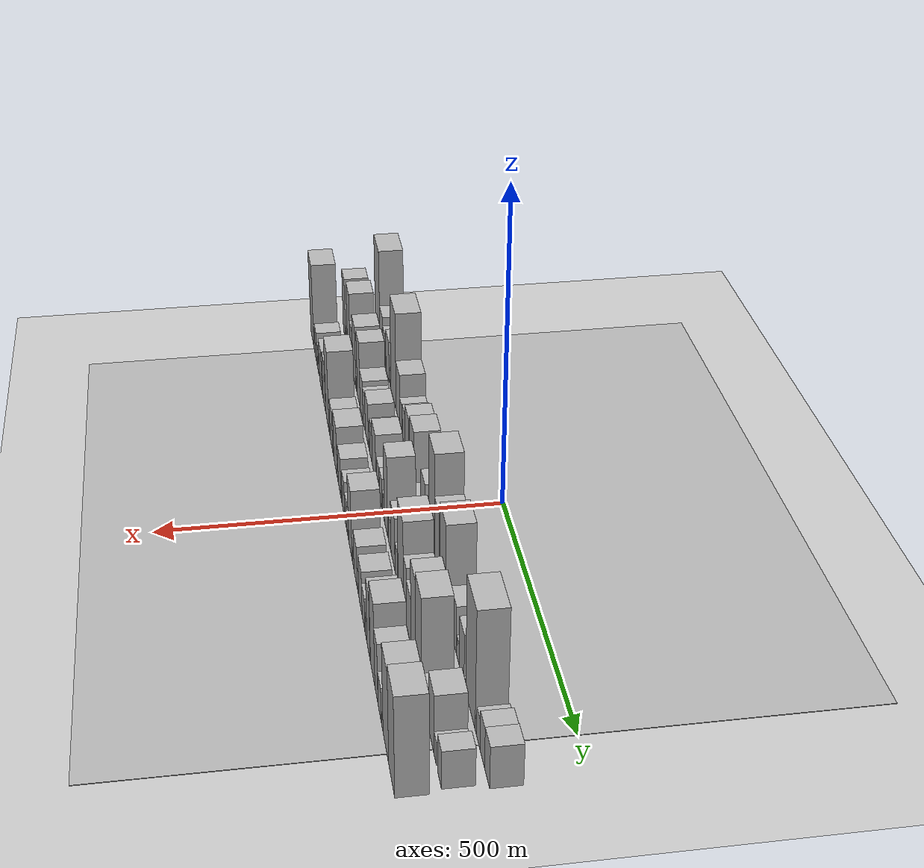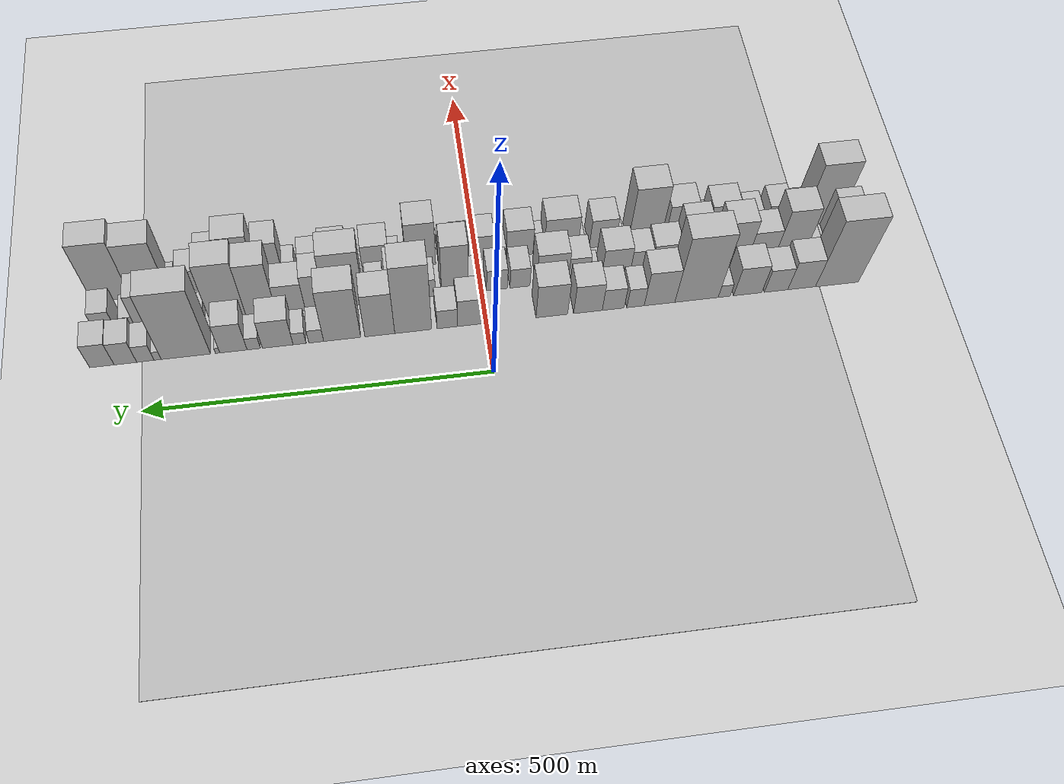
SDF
<?xml version="1.0" encoding="utf-8"?>

<sdf version="1.6">

   <world name="default">

      <gui fullscreen="0">

         <camera name="user_camera">

            <pose>-15 0 4.57585 0 0 0</pose>

            <view_controller>orbit</view_controller>

         </camera>

      </gui>

      <scene>

         <sky>

           <clouds>

             <speed>12</speed>

           </clouds>

         </sky>

         <ambient>0.4 0.4 0.4 1</ambient>

         <background>0.7 0.7 0.7 1</background>

         <shadows>1</shadows>

      </scene>

      <gravity>0 0 -9.8066</gravity>

      <magnetic_field>6e-06 2.3e-05 -4.2e-05</magnetic_field>

      <physics default="0" name="default_physics" type="ode">

         <ode>

            <solver>

               <type>quick</type>

               <iters>10</iters>

               <sor>1.0</sor>

               <use_dynamic_moi_rescaling>0</use_dynamic_moi_rescaling>

            </solver>

            <constraints>

               <cfm>0</cfm>

               <erp>0.2</erp>

               <contact_max_correcting_vel>100</contact_max_correcting_vel>

               <contact_surface_layer>0.001</contact_surface_layer>

            </constraints>

         </ode>

         <max_step_size>0.004</max_step_size>

         <real_time_factor>1</real_time_factor>

         <real_time_update_rate>250</real_time_update_rate>

      </physics>

      <light name="sun" type="directional">

         <cast_shadows>1</cast_shadows>

         <pose>0 0 10 0 0 0</pose>

         <diffuse>0.8 0.8 0.8 1</diffuse>

         <specular>0.2 0.2 0.2 1</specular>

         <attenuation>

            <range>1000</range>

            <constant>0.9</constant>

            <linear>0.01</linear>

            <quadratic>0.001</quadratic>

         </attenuation>

         <direction>-0.5 0.1 -0.9</direction>

      </light>

      <include>

         <name>ground_plane_1</name>

         <uri>model://HANNAS_ground_plane</uri>

         <pose>0 0 0  0 0 0</pose>

      </include>

      <include>

         <name>ground_plane_2</name>

         <uri>model://HANNAS_ground_plane</uri>

         <pose>100 0 0  0 0 0</pose>

      </include>

      <model name="building_1">

         <static>1</static>

         <pose frame="">100.0000 -527.1341 0 0.000000 0.000000 0.000000</pose>

         <link name="link">

            <pose frame="">0 0 87.00 0 0 0</pose>

            <collision name="collision">

               <geometry>

                  <box>

                     <size>40.0000 65.7318 174.0000</size>

                  </box>

               </geometry>

               <max_contacts>10</max_contacts>

               <surface>

                  <contact>

                     <ode/>

                  </contact>

                  <bounce/>

                  <friction>

                     <torsional>

                        <ode/>

                     </torsional>

                     <ode/>

                  </friction>

               </surface>

            </collision>

            <visual name="visual">

               <cast_shadows>0</cast_shadows>

               <geometry>

                  <box>

                     <size>40.0000 65.7318 174.0000</size>

                  </box>

               </geometry>

               <material>

                  <script>

                     <uri>model://HANNAS_wall/materials/scripts</uri>

                     <uri>model://HANNAS_wall/materials/textures</uri>

                     <name>vrc/HANNAS_wall</name>

                  </script>

               </material>

            </visual>

            <self_collide>0</self_collide>

            <enable_wind>0</enable_wind>

            <kinematic>0</kinematic>

         </link>

      </model>

      <model name="building_2">

         <static>1</static>

         <pose frame="">100.0000 -473.0993 0 0.000000 0.000000 0.000000</pose>

         <link name="link">

            <pose frame="">0 0 37.50 0 0 0</pose>

            <collision name="collision">

               <geometry>

                  <box>

                     <size>40.0000 42.3379 75.0000</size>

                  </box>

               </geometry>

               <max_contacts>10</max_contacts>

               <surface>

                  <contact>

                     <ode/>

                  </contact>

                  <bounce/>

                  <friction>

                     <torsional>

                        <ode/>

                     </torsional>

                     <ode/>

                  </friction>

               </surface>

            </collision>

            <visual name="visual">

               <cast_shadows>0</cast_shadows>

               <geometry>

                  <box>

                     <size>40.0000 42.3379 75.0000</size>

                  </box>

               </geometry>

               <material>

                  <script>

                     <uri>model://HANNAS_wall/materials/scripts</uri>

                     <uri>model://HANNAS_wall/materials/textures</uri>

                     <name>vrc/HANNAS_wall</name>

                  </script>

               </material>

            </visual>

            <self_collide>0</self_collide>

            <enable_wind>0</enable_wind>

            <kinematic>0</kinematic>

         </link>

      </model>

      <model name="building_3">

         <static>1</static>

         <pose frame="">100.0000 -434.0599 0 0.000000 0.000000 0.000000</pose>

         <link name="link">

            <pose frame="">0 0 30.00 0 0 0</pose>

            <collision name="collision">

               <geometry>

                  <box>

                     <size>40.0000 35.7409 60.0000</size>

                  </box>

               </geometry>

               <max_contacts>10</max_contacts>

               <surface>

                  <contact>

                     <ode/>

                  </contact>

                  <bounce/>

                  <friction>

                     <torsional>

                        <ode/>

                     </torsional>

                     <ode/>

                  </friction>

               </surface>

            </collision>

            <visual name="visual">

               <cast_shadows>0</cast_shadows>

               <geometry>

                  <box>

                     <size>40.0000 35.7409 60.0000</size>

                  </box>

               </geometry>

               <material>

                  <script>

                     <uri>model://HANNAS_wall/materials/scripts</uri>

                     <uri>model://HANNAS_wall/materials/textures</uri>

                     <name>vrc/HANNAS_wall</name>

                  </script>

               </material>

            </visual>

            <self_collide>0</self_collide>

            <enable_wind>0</enable_wind>

            <kinematic>0</kinematic>

         </link>

      </model>

      <model name="building_4">

         <static>1</static>

         <pose frame="">100.0000 -390.8342 0 0.000000 0.000000 0.000000</pose>

         <link name="link">

            <pose frame="">0 0 37.50 0 0 0</pose>

            <collision name="collision">

               <geometry>

                  <box>

                     <size>40.0000 42.7106 75.0000</size>

                  </box>

               </geometry>

               <max_contacts>10</max_contacts>

               <surface>

                  <contact>

                     <ode/>

                  </contact>

                  <bounce/>

                  <friction>

                     <torsional>

                        <ode/>

                     </torsional>

                     <ode/>

                  </friction>

               </surface>

            </collision>

            <visual name="visual">

               <cast_shadows>0</cast_shadows>

               <geometry>

                  <box>

                     <size>40.0000 42.7106 75.0000</size>

                  </box>

               </geometry>

               <material>

                  <script>

                     <uri>model://HANNAS_wall/materials/scripts</uri>

                     <uri>model://HANNAS_wall/materials/textures</uri>

                     <name>vrc/HANNAS_wall</name>

                  </script>

               </material>

            </visual>

            <self_collide>0</self_collide>

            <enable_wind>0</enable_wind>

            <kinematic>0</kinematic>

         </link>

      </model>

      <model name="building_5">

         <static>1</static>

         <pose frame="">100.0000 -355.3467 0 0.000000 0.000000 0.000000</pose>

         <link name="link">

            <pose frame="">0 0 16.50 0 0 0</pose>

            <collision name="collision">

               <geometry>

                  <box>

                     <size>40.0000 18.2644 33.0000</size>

                  </box>

               </geometry>

               <max_contacts>10</max_contacts>

               <surface>

                  <contact>

                     <ode/>

                  </contact>

                  <bounce/>

                  <friction>

                     <torsional>

                        <ode/>

                     </torsional>

                     <ode/>

                  </friction>

               </surface>

            </collision>

            <visual name="visual">

               <cast_shadows>0</cast_shadows>

               <geometry>

                  <box>

                     <size>40.0000 18.2644 33.0000</size>

                  </box>

               </geometry>

               <material>

                  <script>

                     <uri>model://HANNAS_wall/materials/scripts</uri>

                     <uri>model://HANNAS_wall/materials/textures</uri>

                     <name>vrc/HANNAS_wall</name>

                  </script>

               </material>

            </visual>

            <self_collide>0</self_collide>

            <enable_wind>0</enable_wind>

            <kinematic>0</kinematic>

         </link>

      </model>

      <model name="building_6">

         <static>1</static>

         <pose frame="">100.0000 -313.3908 0 0.000000 0.000000 0.000000</pose>

         <link name="link">

            <pose frame="">0 0 85.50 0 0 0</pose>

            <collision name="collision">

               <geometry>

                  <box>

                     <size>40.0000 65.6473 171.0000</size>

                  </box>

               </geometry>

               <max_contacts>10</max_contacts>

               <surface>

                  <contact>

                     <ode/>

                  </contact>

                  <bounce/>

                  <friction>

                     <torsional>

                        <ode/>

                     </torsional>

                     <ode/>

                  </friction>

               </surface>

            </collision>

            <visual name="visual">

               <cast_shadows>0</cast_shadows>

               <geometry>

                  <box>

                     <size>40.0000 65.6473 171.0000</size>

                  </box>

               </geometry>

               <material>

                  <script>

                     <uri>model://HANNAS_wall/materials/scripts</uri>

                     <uri>model://HANNAS_wall/materials/textures</uri>

                     <name>vrc/HANNAS_wall</name>

                  </script>

               </material>

            </visual>

            <self_collide>0</self_collide>

            <enable_wind>0</enable_wind>

            <kinematic>0</kinematic>

         </link>

      </model>

      <model name="building_7">

         <static>1</static>

         <pose frame="">100.0000 -257.4847 0 0.000000 0.000000 0.000000</pose>

         <link name="link">

            <pose frame="">0 0 45.00 0 0 0</pose>

            <collision name="collision">

               <geometry>

                  <box>

                     <size>40.0000 46.1651 90.0000</size>

                  </box>

               </geometry>

               <max_contacts>10</max_contacts>

               <surface>

                  <contact>

                     <ode/>

                  </contact>

                  <bounce/>

                  <friction>

                     <torsional>

                        <ode/>

                     </torsional>

                     <ode/>

                  </friction>

               </surface>

            </collision>

            <visual name="visual">

               <cast_shadows>0</cast_shadows>

               <geometry>

                  <box>

                     <size>40.0000 46.1651 90.0000</size>

                  </box>

               </geometry>

               <material>

                  <script>

                     <uri>model://HANNAS_wall/materials/scripts</uri>

                     <uri>model://HANNAS_wall/materials/textures</uri>

                     <name>vrc/HANNAS_wall</name>

                  </script>

               </material>

            </visual>

            <self_collide>0</self_collide>

            <enable_wind>0</enable_wind>

            <kinematic>0</kinematic>

         </link>

      </model>

      <model name="building_8">

         <static>1</static>

         <pose frame="">100.0000 -221.3665 0 0.000000 0.000000 0.000000</pose>

         <link name="link">

            <pose frame="">0 0 25.50 0 0 0</pose>

            <collision name="collision">

               <geometry>

                  <box>

                     <size>40.0000 26.0713 51.0000</size>

                  </box>

               </geometry>

               <max_contacts>10</max_contacts>

               <surface>

                  <contact>

                     <ode/>

                  </contact>

                  <bounce/>

                  <friction>

                     <torsional>

                        <ode/>

                     </torsional>

                     <ode/>

                  </friction>

               </surface>

            </collision>

            <visual name="visual">

               <cast_shadows>0</cast_shadows>

               <geometry>

                  <box>

                     <size>40.0000 26.0713 51.0000</size>

                  </box>

               </geometry>

               <material>

                  <script>

                     <uri>model://HANNAS_wall/materials/scripts</uri>

                     <uri>model://HANNAS_wall/materials/textures</uri>

                     <name>vrc/HANNAS_wall</name>

                  </script>

               </material>

            </visual>

            <self_collide>0</self_collide>

            <enable_wind>0</enable_wind>

            <kinematic>0</kinematic>

         </link>

      </model>

      <model name="building_9">

         <static>1</static>

         <pose frame="">100.0000 -187.9734 0 0.000000 0.000000 0.000000</pose>

         <link name="link">

            <pose frame="">0 0 28.50 0 0 0</pose>

            <collision name="collision">

               <geometry>

                  <box>

                     <size>40.0000 32.7148 57.0000</size>

                  </box>

               </geometry>

               <max_contacts>10</max_contacts>

               <surface>

                  <contact>

                     <ode/>

                  </contact>

                  <bounce/>

                  <friction>

                     <torsional>

                        <ode/>

                     </torsional>

                     <ode/>

                  </friction>

               </surface>

            </collision>

            <visual name="visual">

               <cast_shadows>0</cast_shadows>

               <geometry>

                  <box>

                     <size>40.0000 32.7148 57.0000</size>

                  </box>

               </geometry>

               <material>

                  <script>

                     <uri>model://HANNAS_wall/materials/scripts</uri>

                     <uri>model://HANNAS_wall/materials/textures</uri>

                     <name>vrc/HANNAS_wall</name>

                  </script>

               </material>

            </visual>

            <self_collide>0</self_collide>

            <enable_wind>0</enable_wind>

            <kinematic>0</kinematic>

         </link>

      </model>

      <model name="building_10">

         <static>1</static>

         <pose frame="">100.0000 -150.2736 0 0.000000 0.000000 0.000000</pose>

         <link name="link">

            <pose frame="">0 0 37.50 0 0 0</pose>

            <collision name="collision">

               <geometry>

                  <box>

                     <size>40.0000 42.6848 75.0000</size>

                  </box>

               </geometry>

               <max_contacts>10</max_contacts>

               <surface>

                  <contact>

                     <ode/>

                  </contact>

                  <bounce/>

                  <friction>

                     <torsional>

                        <ode/>

                     </torsional>

                     <ode/>

                  </friction>

               </surface>

            </collision>

            <visual name="visual">

               <cast_shadows>0</cast_shadows>

               <geometry>

                  <box>

                     <size>40.0000 42.6848 75.0000</size>

                  </box>

               </geometry>

               <material>

                  <script>

                     <uri>model://HANNAS_wall/materials/scripts</uri>

                     <uri>model://HANNAS_wall/materials/textures</uri>

                     <name>vrc/HANNAS_wall</name>

                  </script>

               </material>

            </visual>

            <self_collide>0</self_collide>

            <enable_wind>0</enable_wind>

            <kinematic>0</kinematic>

         </link>

      </model>

      <model name="building_11">

         <static>1</static>

         <pose frame="">100.0000 -96.4146 0 0.000000 0.000000 0.000000</pose>

         <link name="link">

            <pose frame="">0 0 43.50 0 0 0</pose>

            <collision name="collision">

               <geometry>

                  <box>

                     <size>40.0000 47.0333 87.0000</size>

                  </box>

               </geometry>

               <max_contacts>10</max_contacts>

               <surface>

                  <contact>

                     <ode/>

                  </contact>

                  <bounce/>

                  <friction>

                     <torsional>

                        <ode/>

                     </torsional>

                     <ode/>

                  </friction>

               </surface>

            </collision>

            <visual name="visual">

               <cast_shadows>0</cast_shadows>

               <geometry>

                  <box>

                     <size>40.0000 47.0333 87.0000</size>

                  </box>

               </geometry>

               <material>

                  <script>

                     <uri>model://HANNAS_wall/materials/scripts</uri>

                     <uri>model://HANNAS_wall/materials/textures</uri>

                     <name>vrc/HANNAS_wall</name>

                  </script>

               </material>

            </visual>

            <self_collide>0</self_collide>

            <enable_wind>0</enable_wind>

            <kinematic>0</kinematic>

         </link>

      </model>

      <model name="building_12">

         <static>1</static>

         <pose frame="">100.0000 22.2262 0 0.000000 0.000000 0.000000</pose>

         <link name="link">

            <pose frame="">0 0 36.00 0 0 0</pose>

            <collision name="collision">

               <geometry>

                  <box>

                     <size>40.0000 41.4161 72.0000</size>

                  </box>

               </geometry>

               <max_contacts>10</max_contacts>

               <surface>

                  <contact>

                     <ode/>

                  </contact>

                  <bounce/>

                  <friction>

                     <torsional>

                        <ode/>

                     </torsional>

                     <ode/>

                  </friction>

               </surface>

            </collision>

            <visual name="visual">

               <cast_shadows>0</cast_shadows>

               <geometry>

                  <box>

                     <size>40.0000 41.4161 72.0000</size>

                  </box>

               </geometry>

               <material>

                  <script>

                     <uri>model://HANNAS_wall/materials/scripts</uri>

                     <uri>model://HANNAS_wall/materials/textures</uri>

                     <name>vrc/HANNAS_wall</name>

                  </script>

               </material>

            </visual>

            <self_collide>0</self_collide>

            <enable_wind>0</enable_wind>

            <kinematic>0</kinematic>

         </link>

      </model>

      <model name="building_13">

         <static>1</static>

         <pose frame="">100.0000 58.0329 0 0.000000 0.000000 0.000000</pose>

         <link name="link">

            <pose frame="">0 0 25.50 0 0 0</pose>

            <collision name="collision">

               <geometry>

                  <box>

                     <size>40.0000 30.1973 51.0000</size>

                  </box>

               </geometry>

               <max_contacts>10</max_contacts>

               <surface>

                  <contact>

                     <ode/>

                  </contact>

                  <bounce/>

                  <friction>

                     <torsional>

                        <ode/>

                     </torsional>

                     <ode/>

                  </friction>

               </surface>

            </collision>

            <visual name="visual">

               <cast_shadows>0</cast_shadows>

               <geometry>

                  <box>

                     <size>40.0000 30.1973 51.0000</size>

                  </box>

               </geometry>

               <material>

                  <script>

                     <uri>model://HANNAS_wall/materials/scripts</uri>

                     <uri>model://HANNAS_wall/materials/textures</uri>

                     <name>vrc/HANNAS_wall</name>

                  </script>

               </material>

            </visual>

            <self_collide>0</self_collide>

            <enable_wind>0</enable_wind>

            <kinematic>0</kinematic>

         </link>

      </model>

      <model name="building_14">

         <static>1</static>

         <pose frame="">100.0000 108.1731 0 0.000000 0.000000 0.000000</pose>

         <link name="link">

            <pose frame="">0 0 90.00 0 0 0</pose>

            <collision name="collision">

               <geometry>

                  <box>

                     <size>40.0000 54.0830 180.0000</size>

                  </box>

               </geometry>

               <max_contacts>10</max_contacts>

               <surface>

                  <contact>

                     <ode/>

                  </contact>

                  <bounce/>

                  <friction>

                     <torsional>

                        <ode/>

                     </torsional>

                     <ode/>

                  </friction>

               </surface>

            </collision>

            <visual name="visual">

               <cast_shadows>0</cast_shadows>

               <geometry>

                  <box>

                     <size>40.0000 54.0830 180.0000</size>

                  </box>

               </geometry>

               <material>

                  <script>

                     <uri>model://HANNAS_wall/materials/scripts</uri>

                     <uri>model://HANNAS_wall/materials/textures</uri>

                     <name>vrc/HANNAS_wall</name>

                  </script>

               </material>

            </visual>

            <self_collide>0</self_collide>

            <enable_wind>0</enable_wind>

            <kinematic>0</kinematic>

         </link>

      </model>

      <model name="building_15">

         <static>1</static>

         <pose frame="">100.0000 157.1186 0 0.000000 0.000000 0.000000</pose>

         <link name="link">

            <pose frame="">0 0 57.00 0 0 0</pose>

            <collision name="collision">

               <geometry>

                  <box>

                     <size>40.0000 43.8080 114.0000</size>

                  </box>

               </geometry>

               <max_contacts>10</max_contacts>

               <surface>

                  <contact>

                     <ode/>

                  </contact>

                  <bounce/>

                  <friction>

                     <torsional>

                        <ode/>

                     </torsional>

                     <ode/>

                  </friction>

               </surface>

            </collision>

            <visual name="visual">

               <cast_shadows>0</cast_shadows>

               <geometry>

                  <box>

                     <size>40.0000 43.8080 114.0000</size>

                  </box>

               </geometry>

               <material>

                  <script>

                     <uri>model://HANNAS_wall/materials/scripts</uri>

                     <uri>model://HANNAS_wall/materials/textures</uri>

                     <name>vrc/HANNAS_wall</name>

                  </script>

               </material>

            </visual>

            <self_collide>0</self_collide>

            <enable_wind>0</enable_wind>

            <kinematic>0</kinematic>

         </link>

      </model>

      <model name="building_16">

         <static>1</static>

         <pose frame="">100.0000 211.9651 0 0.000000 0.000000 0.000000</pose>

         <link name="link">

            <pose frame="">0 0 69.00 0 0 0</pose>

            <collision name="collision">

               <geometry>

                  <box>

                     <size>40.0000 53.8850 138.0000</size>

                  </box>

               </geometry>

               <max_contacts>10</max_contacts>

               <surface>

                  <contact>

                     <ode/>

                  </contact>

                  <bounce/>

                  <friction>

                     <torsional>

                        <ode/>

                     </torsional>

                     <ode/>

                  </friction>

               </surface>

            </collision>

            <visual name="visual">

               <cast_shadows>0</cast_shadows>

               <geometry>

                  <box>

                     <size>40.0000 53.8850 138.0000</size>

                  </box>

               </geometry>

               <material>

                  <script>

                     <uri>model://HANNAS_wall/materials/scripts</uri>

                     <uri>model://HANNAS_wall/materials/textures</uri>

                     <name>vrc/HANNAS_wall</name>

                  </script>

               </material>

            </visual>

            <self_collide>0</self_collide>

            <enable_wind>0</enable_wind>

            <kinematic>0</kinematic>

         </link>

      </model>

      <model name="building_17">

         <static>1</static>

         <pose frame="">100.0000 249.6455 0 0.000000 0.000000 0.000000</pose>

         <link name="link">

            <pose frame="">0 0 18.00 0 0 0</pose>

            <collision name="collision">

               <geometry>

                  <box>

                     <size>40.0000 21.4758 36.0000</size>

                  </box>

               </geometry>

               <max_contacts>10</max_contacts>

               <surface>

                  <contact>

                     <ode/>

                  </contact>

                  <bounce/>

                  <friction>

                     <torsional>

                        <ode/>

                     </torsional>

                     <ode/>

                  </friction>

               </surface>

            </collision>

            <visual name="visual">

               <cast_shadows>0</cast_shadows>

               <geometry>

                  <box>

                     <size>40.0000 21.4758 36.0000</size>

                  </box>

               </geometry>

               <material>

                  <script>

                     <uri>model://HANNAS_wall/materials/scripts</uri>

                     <uri>model://HANNAS_wall/materials/textures</uri>

                     <name>vrc/HANNAS_wall</name>

                  </script>

               </material>

            </visual>

            <self_collide>0</self_collide>

            <enable_wind>0</enable_wind>

            <kinematic>0</kinematic>

         </link>

      </model>

      <model name="building_18">

         <static>1</static>

         <pose frame="">100.0000 273.7576 0 0.000000 0.000000 0.000000</pose>

         <link name="link">

            <pose frame="">0 0 16.50 0 0 0</pose>

            <collision name="collision">

               <geometry>

                  <box>

                     <size>40.0000 18.7484 33.0000</size>

                  </box>

               </geometry>

               <max_contacts>10</max_contacts>

               <surface>

                  <contact>

                     <ode/>

                  </contact>

                  <bounce/>

                  <friction>

                     <torsional>

                        <ode/>

                     </torsional>

                     <ode/>

                  </friction>

               </surface>

            </collision>

            <visual name="visual">

               <cast_shadows>0</cast_shadows>

               <geometry>

                  <box>

                     <size>40.0000 18.7484 33.0000</size>

                  </box>

               </geometry>

               <material>

                  <script>

                     <uri>model://HANNAS_wall/materials/scripts</uri>

                     <uri>model://HANNAS_wall/materials/textures</uri>

                     <name>vrc/HANNAS_wall</name>

                  </script>

               </material>

            </visual>

            <self_collide>0</self_collide>

            <enable_wind>0</enable_wind>

            <kinematic>0</kinematic>

         </link>

      </model>

      <model name="building_19">

         <static>1</static>

         <pose frame="">100.0000 305.3398 0 0.000000 0.000000 0.000000</pose>

         <link name="link">

            <pose frame="">0 0 37.50 0 0 0</pose>

            <collision name="collision">

               <geometry>

                  <box>

                     <size>40.0000 44.4159 75.0000</size>

                  </box>

               </geometry>

               <max_contacts>10</max_contacts>

               <surface>

                  <contact>

                     <ode/>

                  </contact>

                  <bounce/>

                  <friction>

                     <torsional>

                        <ode/>

                     </torsional>

                     <ode/>

                  </friction>

               </surface>

            </collision>

            <visual name="visual">

               <cast_shadows>0</cast_shadows>

               <geometry>

                  <box>

                     <size>40.0000 44.4159 75.0000</size>

                  </box>

               </geometry>

               <material>

                  <script>

                     <uri>model://HANNAS_wall/materials/scripts</uri>

                     <uri>model://HANNAS_wall/materials/textures</uri>

                     <name>vrc/HANNAS_wall</name>

                  </script>

               </material>

            </visual>

            <self_collide>0</self_collide>

            <enable_wind>0</enable_wind>

            <kinematic>0</kinematic>

         </link>

      </model>

      <model name="building_20">

         <static>1</static>

         <pose frame="">100.0000 340.0875 0 0.000000 0.000000 0.000000</pose>

         <link name="link">

            <pose frame="">0 0 16.50 0 0 0</pose>

            <collision name="collision">

               <geometry>

                  <box>

                     <size>40.0000 19.0794 33.0000</size>

                  </box>

               </geometry>

               <max_contacts>10</max_contacts>

               <surface>

                  <contact>

                     <ode/>

                  </contact>

                  <bounce/>

                  <friction>

                     <torsional>

                        <ode/>

                     </torsional>

                     <ode/>

                  </friction>

               </surface>

            </collision>

            <visual name="visual">

               <cast_shadows>0</cast_shadows>

               <geometry>

                  <box>

                     <size>40.0000 19.0794 33.0000</size>

                  </box>

               </geometry>

               <material>

                  <script>

                     <uri>model://HANNAS_wall/materials/scripts</uri>

                     <uri>model://HANNAS_wall/materials/textures</uri>

                     <name>vrc/HANNAS_wall</name>

                  </script>

               </material>

            </visual>

            <self_collide>0</self_collide>

            <enable_wind>0</enable_wind>

            <kinematic>0</kinematic>

         </link>

      </model>

      <model name="building_21">

         <static>1</static>

         <pose frame="">100.0000 369.3502 0 0.000000 0.000000 0.000000</pose>

         <link name="link">

            <pose frame="">0 0 39.00 0 0 0</pose>

            <collision name="collision">

               <geometry>

                  <box>

                     <size>40.0000 39.4459 78.0000</size>

                  </box>

               </geometry>

               <max_contacts>10</max_contacts>

               <surface>

                  <contact>

                     <ode/>

                  </contact>

                  <bounce/>

                  <friction>

                     <torsional>

                        <ode/>

                     </torsional>

                     <ode/>

                  </friction>

               </surface>

            </collision>

            <visual name="visual">

               <cast_shadows>0</cast_shadows>

               <geometry>

                  <box>

                     <size>40.0000 39.4459 78.0000</size>

                  </box>

               </geometry>

               <material>

                  <script>

                     <uri>model://HANNAS_wall/materials/scripts</uri>

                     <uri>model://HANNAS_wall/materials/textures</uri>

                     <name>vrc/HANNAS_wall</name>

                  </script>

               </material>

            </visual>

            <self_collide>0</self_collide>

            <enable_wind>0</enable_wind>

            <kinematic>0</kinematic>

         </link>

      </model>

      <model name="building_22">

         <static>1</static>

         <pose frame="">100.0000 392.1713 0 0.000000 0.000000 0.000000</pose>

         <link name="link">

            <pose frame="">0 0 7.50 0 0 0</pose>

            <collision name="collision">

               <geometry>

                  <box>

                     <size>40.0000 6.1963 15.0000</size>

                  </box>

               </geometry>

               <max_contacts>10</max_contacts>

               <surface>

                  <contact>

                     <ode/>

                  </contact>

                  <bounce/>

                  <friction>

                     <torsional>

                        <ode/>

                     </torsional>

                     <ode/>

                  </friction>

               </surface>

            </collision>

            <visual name="visual">

               <cast_shadows>0</cast_shadows>

               <geometry>

                  <box>

                     <size>40.0000 6.1963 15.0000</size>

                  </box>

               </geometry>

               <material>

                  <script>

                     <uri>model://HANNAS_wall/materials/scripts</uri>

                     <uri>model://HANNAS_wall/materials/textures</uri>

                     <name>vrc/HANNAS_wall</name>

                  </script>

               </material>

            </visual>

            <self_collide>0</self_collide>

            <enable_wind>0</enable_wind>

            <kinematic>0</kinematic>

         </link>

      </model>

      <model name="building_23">

         <static>1</static>

         <pose frame="">100.0000 437.7025 0 0.000000 0.000000 0.000000</pose>

         <link name="link">

            <pose frame="">0 0 90.00 0 0 0</pose>

            <collision name="collision">

               <geometry>

                  <box>

                     <size>40.0000 70.8663 180.0000</size>

                  </box>

               </geometry>

               <max_contacts>10</max_contacts>

               <surface>

                  <contact>

                     <ode/>

                  </contact>

                  <bounce/>

                  <friction>

                     <torsional>

                        <ode/>

                     </torsional>

                     <ode/>

                  </friction>

               </surface>

            </collision>

            <visual name="visual">

               <cast_shadows>0</cast_shadows>

               <geometry>

                  <box>

                     <size>40.0000 70.8663 180.0000</size>

                  </box>

               </geometry>

               <material>

                  <script>

                     <uri>model://HANNAS_wall/materials/scripts</uri>

                     <uri>model://HANNAS_wall/materials/textures</uri>

                     <name>vrc/HANNAS_wall</name>

                  </script>

               </material>

            </visual>

            <self_collide>0</self_collide>

            <enable_wind>0</enable_wind>

            <kinematic>0</kinematic>

         </link>

      </model>

      <model name="building_24">

         <static>1</static>

         <pose frame="">100.0000 478.2067 0 0.000000 0.000000 0.000000</pose>

         <link name="link">

            <pose frame="">0 0 12.00 0 0 0</pose>

            <collision name="collision">

               <geometry>

                  <box>

                     <size>40.0000 10.1421 24.0000</size>

                  </box>

               </geometry>

               <max_contacts>10</max_contacts>

               <surface>

                  <contact>

                     <ode/>

                  </contact>

                  <bounce/>

                  <friction>

                     <torsional>

                        <ode/>

                     </torsional>

                     <ode/>

                  </friction>

               </surface>

            </collision>

            <visual name="visual">

               <cast_shadows>0</cast_shadows>

               <geometry>

                  <box>

                     <size>40.0000 10.1421 24.0000</size>

                  </box>

               </geometry>

               <material>

                  <script>

                     <uri>model://HANNAS_wall/materials/scripts</uri>

                     <uri>model://HANNAS_wall/materials/textures</uri>

                     <name>vrc/HANNAS_wall</name>

                  </script>

               </material>

            </visual>

            <self_collide>0</self_collide>

            <enable_wind>0</enable_wind>

            <kinematic>0</kinematic>

         </link>

      </model>

      <model name="building_25">

         <static>1</static>

         <pose frame="">100.0000 495.6289 0 0.000000 0.000000 0.000000</pose>

         <link name="link">

            <pose frame="">0 0 22.50 0 0 0</pose>

            <collision name="collision">

               <geometry>

                  <box>

                     <size>40.0000 24.7021 45.0000</size>

                  </box>

               </geometry>

               <max_contacts>10</max_contacts>

               <surface>

                  <contact>

                     <ode/>

                  </contact>

                  <bounce/>

                  <friction>

                     <torsional>

                        <ode/>

                     </torsional>

                     <ode/>

                  </friction>

               </surface>

            </collision>

            <visual name="visual">

               <cast_shadows>0</cast_shadows>

               <geometry>

                  <box>

                     <size>40.0000 24.7021 45.0000</size>

                  </box>

               </geometry>

               <material>

                  <script>

                     <uri>model://HANNAS_wall/materials/scripts</uri>

                     <uri>model://HANNAS_wall/materials/textures</uri>

                     <name>vrc/HANNAS_wall</name>

                  </script>

               </material>

            </visual>

            <self_collide>0</self_collide>

            <enable_wind>0</enable_wind>

            <kinematic>0</kinematic>

         </link>

      </model>

      <model name="building_26">

         <static>1</static>

         <pose frame="">100.0000 524.0580 0 0.000000 0.000000 0.000000</pose>

         <link name="link">

            <pose frame="">0 0 30.00 0 0 0</pose>

            <collision name="collision">

               <geometry>

                  <box>

                     <size>40.0000 32.1562 60.0000</size>

                  </box>

               </geometry>

               <max_contacts>10</max_contacts>

               <surface>

                  <contact>

                     <ode/>

                  </contact>

                  <bounce/>

                  <friction>

                     <torsional>

                        <ode/>

                     </torsional>

                     <ode/>

                  </friction>

               </surface>

            </collision>

            <visual name="visual">

               <cast_shadows>0</cast_shadows>

               <geometry>

                  <box>

                     <size>40.0000 32.1562 60.0000</size>

                  </box>

               </geometry>

               <material>

                  <script>

                     <uri>model://HANNAS_wall/materials/scripts</uri>

                     <uri>model://HANNAS_wall/materials/textures</uri>

                     <name>vrc/HANNAS_wall</name>

                  </script>

               </material>

            </visual>

            <self_collide>0</self_collide>

            <enable_wind>0</enable_wind>

            <kinematic>0</kinematic>

         </link>

      </model>

      <model name="building_27">

         <static>1</static>

         <pose frame="">100.0000 557.5274 0 0.000000 0.000000 0.000000</pose>

         <link name="link">

            <pose frame="">0 0 31.50 0 0 0</pose>

            <collision name="collision">

               <geometry>

                  <box>

                     <size>40.0000 34.7827 63.0000</size>

                  </box>

               </geometry>

               <max_contacts>10</max_contacts>

               <surface>

                  <contact>

                     <ode/>

                  </contact>

                  <bounce/>

                  <friction>

                     <torsional>

                        <ode/>

                     </torsional>

                     <ode/>

                  </friction>

               </surface>

            </collision>

            <visual name="visual">

               <cast_shadows>0</cast_shadows>

               <geometry>

                  <box>

                     <size>40.0000 34.7827 63.0000</size>

                  </box>

               </geometry>

               <material>

                  <script>

                     <uri>model://HANNAS_wall/materials/scripts</uri>

                     <uri>model://HANNAS_wall/materials/textures</uri>

                     <name>vrc/HANNAS_wall</name>

                  </script>

               </material>

            </visual>

            <self_collide>0</self_collide>

            <enable_wind>0</enable_wind>

            <kinematic>0</kinematic>

         </link>

      </model>

      <model name="building_28">

         <static>1</static>

         <pose frame="">155.0000 -540.9179 0 0.000000 0.000000 0.000000</pose>

         <link name="link">

            <pose frame="">0 0 57.00 0 0 0</pose>

            <collision name="collision">

               <geometry>

                  <box>

                     <size>40.0000 38.1643 114.0000</size>

                  </box>

               </geometry>

               <max_contacts>10</max_contacts>

               <surface>

                  <contact>

                     <ode/>

                  </contact>

                  <bounce/>

                  <friction>

                     <torsional>

                        <ode/>

                     </torsional>

                     <ode/>

                  </friction>

               </surface>

            </collision>

            <visual name="visual">

               <cast_shadows>0</cast_shadows>

               <geometry>

                  <box>

                     <size>40.0000 38.1643 114.0000</size>

                  </box>

               </geometry>

               <material>

                  <script>

                     <uri>model://HANNAS_wall/materials/scripts</uri>

                     <uri>model://HANNAS_wall/materials/textures</uri>

                     <name>vrc/HANNAS_wall</name>

                  </script>

               </material>

            </visual>

            <self_collide>0</self_collide>

            <enable_wind>0</enable_wind>

            <kinematic>0</kinematic>

         </link>

      </model>

      <model name="building_29">

         <static>1</static>

         <pose frame="">155.0000 -517.1502 0 0.000000 0.000000 0.000000</pose>

         <link name="link">

            <pose frame="">0 0 10.50 0 0 0</pose>

            <collision name="collision">

               <geometry>

                  <box>

                     <size>40.0000 9.3711 21.0000</size>

                  </box>

               </geometry>

               <max_contacts>10</max_contacts>

               <surface>

                  <contact>

                     <ode/>

                  </contact>

                  <bounce/>

                  <friction>

                     <torsional>

                        <ode/>

                     </torsional>

                     <ode/>

                  </friction>

               </surface>

            </collision>

            <visual name="visual">

               <cast_shadows>0</cast_shadows>

               <geometry>

                  <box>

                     <size>40.0000 9.3711 21.0000</size>

                  </box>

               </geometry>

               <material>

                  <script>

                     <uri>model://HANNAS_wall/materials/scripts</uri>

                     <uri>model://HANNAS_wall/materials/textures</uri>

                     <name>vrc/HANNAS_wall</name>

                  </script>

               </material>

            </visual>

            <self_collide>0</self_collide>

            <enable_wind>0</enable_wind>

            <kinematic>0</kinematic>

         </link>

      </model>

      <model name="building_30">

         <static>1</static>

         <pose frame="">155.0000 -503.4200 0 0.000000 0.000000 0.000000</pose>

         <link name="link">

            <pose frame="">0 0 16.50 0 0 0</pose>

            <collision name="collision">

               <geometry>

                  <box>

                     <size>40.0000 18.0893 33.0000</size>

                  </box>

               </geometry>

               <max_contacts>10</max_contacts>

               <surface>

                  <contact>

                     <ode/>

                  </contact>

                  <bounce/>

                  <friction>

                     <torsional>

                        <ode/>

                     </torsional>

                     <ode/>

                  </friction>

               </surface>

            </collision>

            <visual name="visual">

               <cast_shadows>0</cast_shadows>

               <geometry>

                  <box>

                     <size>40.0000 18.0893 33.0000</size>

                  </box>

               </geometry>

               <material>

                  <script>

                     <uri>model://HANNAS_wall/materials/scripts</uri>

                     <uri>model://HANNAS_wall/materials/textures</uri>

                     <name>vrc/HANNAS_wall</name>

                  </script>

               </material>

            </visual>

            <self_collide>0</self_collide>

            <enable_wind>0</enable_wind>

            <kinematic>0</kinematic>

         </link>

      </model>

      <model name="building_31">

         <static>1</static>

         <pose frame="">155.0000 -467.3624 0 0.000000 0.000000 0.000000</pose>

         <link name="link">

            <pose frame="">0 0 63.00 0 0 0</pose>

            <collision name="collision">

               <geometry>

                  <box>

                     <size>40.0000 46.0259 126.0000</size>

                  </box>

               </geometry>

               <max_contacts>10</max_contacts>

               <surface>

                  <contact>

                     <ode/>

                  </contact>

                  <bounce/>

                  <friction>

                     <torsional>

                        <ode/>

                     </torsional>

                     <ode/>

                  </friction>

               </surface>

            </collision>

            <visual name="visual">

               <cast_shadows>0</cast_shadows>

               <geometry>

                  <box>

                     <size>40.0000 46.0259 126.0000</size>

                  </box>

               </geometry>

               <material>

                  <script>

                     <uri>model://HANNAS_wall/materials/scripts</uri>

                     <uri>model://HANNAS_wall/materials/textures</uri>

                     <name>vrc/HANNAS_wall</name>

                  </script>

               </material>

            </visual>

            <self_collide>0</self_collide>

            <enable_wind>0</enable_wind>

            <kinematic>0</kinematic>

         </link>

      </model>

      <model name="building_32">

         <static>1</static>

         <pose frame="">155.0000 -423.4653 0 0.000000 0.000000 0.000000</pose>

         <link name="link">

            <pose frame="">0 0 39.00 0 0 0</pose>

            <collision name="collision">

               <geometry>

                  <box>

                     <size>40.0000 41.7684 78.0000</size>

                  </box>

               </geometry>

               <max_contacts>10</max_contacts>

               <surface>

                  <contact>

                     <ode/>

                  </contact>

                  <bounce/>

                  <friction>

                     <torsional>

                        <ode/>

                     </torsional>

                     <ode/>

                  </friction>

               </surface>

            </collision>

            <visual name="visual">

               <cast_shadows>0</cast_shadows>

               <geometry>

                  <box>

                     <size>40.0000 41.7684 78.0000</size>

                  </box>

               </geometry>

               <material>

                  <script>

                     <uri>model://HANNAS_wall/materials/scripts</uri>

                     <uri>model://HANNAS_wall/materials/textures</uri>

                     <name>vrc/HANNAS_wall</name>

                  </script>

               </material>

            </visual>

            <self_collide>0</self_collide>

            <enable_wind>0</enable_wind>

            <kinematic>0</kinematic>

         </link>

      </model>

      <model name="building_33">

         <static>1</static>

         <pose frame="">155.0000 -380.6023 0 0.000000 0.000000 0.000000</pose>

         <link name="link">

            <pose frame="">0 0 55.50 0 0 0</pose>

            <collision name="collision">

               <geometry>

                  <box>

                     <size>40.0000 43.9575 111.0000</size>

                  </box>

               </geometry>

               <max_contacts>10</max_contacts>

               <surface>

                  <contact>

                     <ode/>

                  </contact>

                  <bounce/>

                  <friction>

                     <torsional>

                        <ode/>

                     </torsional>

                     <ode/>

                  </friction>

               </surface>

            </collision>

            <visual name="visual">

               <cast_shadows>0</cast_shadows>

               <geometry>

                  <box>

                     <size>40.0000 43.9575 111.0000</size>

                  </box>

               </geometry>

               <material>

                  <script>

                     <uri>model://HANNAS_wall/materials/scripts</uri>

                     <uri>model://HANNAS_wall/materials/textures</uri>

                     <name>vrc/HANNAS_wall</name>

                  </script>

               </material>

            </visual>

            <self_collide>0</self_collide>

            <enable_wind>0</enable_wind>

            <kinematic>0</kinematic>

         </link>

      </model>

      <model name="building_34">

         <static>1</static>

         <pose frame="">155.0000 -352.1251 0 0.000000 0.000000 0.000000</pose>

         <link name="link">

            <pose frame="">0 0 13.50 0 0 0</pose>

            <collision name="collision">

               <geometry>

                  <box>

                     <size>40.0000 12.9970 27.0000</size>

                  </box>

               </geometry>

               <max_contacts>10</max_contacts>

               <surface>

                  <contact>

                     <ode/>

                  </contact>

                  <bounce/>

                  <friction>

                     <torsional>

                        <ode/>

                     </torsional>

                     <ode/>

                  </friction>

               </surface>

            </collision>

            <visual name="visual">

               <cast_shadows>0</cast_shadows>

               <geometry>

                  <box>

                     <size>40.0000 12.9970 27.0000</size>

                  </box>

               </geometry>

               <material>

                  <script>

                     <uri>model://HANNAS_wall/materials/scripts</uri>

                     <uri>model://HANNAS_wall/materials/textures</uri>

                     <name>vrc/HANNAS_wall</name>

                  </script>

               </material>

            </visual>

            <self_collide>0</self_collide>

            <enable_wind>0</enable_wind>

            <kinematic>0</kinematic>

         </link>

      </model>

      <model name="building_35">

         <static>1</static>

         <pose frame="">155.0000 -341.3082 0 0.000000 0.000000 0.000000</pose>

         <link name="link">

            <pose frame="">0 0 9.00 0 0 0</pose>

            <collision name="collision">

               <geometry>

                  <box>

                     <size>40.0000 8.6367 18.0000</size>

                  </box>

               </geometry>

               <max_contacts>10</max_contacts>

               <surface>

                  <contact>

                     <ode/>

                  </contact>

                  <bounce/>

                  <friction>

                     <torsional>

                        <ode/>

                     </torsional>

                     <ode/>

                  </friction>

               </surface>

            </collision>

            <visual name="visual">

               <cast_shadows>0</cast_shadows>

               <geometry>

                  <box>

                     <size>40.0000 8.6367 18.0000</size>

                  </box>

               </geometry>

               <material>

                  <script>

                     <uri>model://HANNAS_wall/materials/scripts</uri>

                     <uri>model://HANNAS_wall/materials/textures</uri>

                     <name>vrc/HANNAS_wall</name>

                  </script>

               </material>

            </visual>

            <self_collide>0</self_collide>

            <enable_wind>0</enable_wind>

            <kinematic>0</kinematic>

         </link>

      </model>

      <model name="building_36">

         <static>1</static>

         <pose frame="">155.0000 -316.5305 0 0.000000 0.000000 0.000000</pose>

         <link name="link">

            <pose frame="">0 0 58.50 0 0 0</pose>

            <collision name="collision">

               <geometry>

                  <box>

                     <size>40.0000 40.9187 117.0000</size>

                  </box>

               </geometry>

               <max_contacts>10</max_contacts>

               <surface>

                  <contact>

                     <ode/>

                  </contact>

                  <bounce/>

                  <friction>

                     <torsional>

                        <ode/>

                     </torsional>

                     <ode/>

                  </friction>

               </surface>

            </collision>

            <visual name="visual">

               <cast_shadows>0</cast_shadows>

               <geometry>

                  <box>

                     <size>40.0000 40.9187 117.0000</size>

                  </box>

               </geometry>

               <material>

                  <script>

                     <uri>model://HANNAS_wall/materials/scripts</uri>

                     <uri>model://HANNAS_wall/materials/textures</uri>

                     <name>vrc/HANNAS_wall</name>

                  </script>

               </material>

            </visual>

            <self_collide>0</self_collide>

            <enable_wind>0</enable_wind>

            <kinematic>0</kinematic>

         </link>

      </model>

      <model name="building_37">

         <static>1</static>

         <pose frame="">155.0000 -275.3972 0 0.000000 0.000000 0.000000</pose>

         <link name="link">

            <pose frame="">0 0 36.00 0 0 0</pose>

            <collision name="collision">

               <geometry>

                  <box>

                     <size>40.0000 41.3480 72.0000</size>

                  </box>

               </geometry>

               <max_contacts>10</max_contacts>

               <surface>

                  <contact>

                     <ode/>

                  </contact>

                  <bounce/>

                  <friction>

                     <torsional>

                        <ode/>

                     </torsional>

                     <ode/>

                  </friction>

               </surface>

            </collision>

            <visual name="visual">

               <cast_shadows>0</cast_shadows>

               <geometry>

                  <box>

                     <size>40.0000 41.3480 72.0000</size>

                  </box>

               </geometry>

               <material>

                  <script>

                     <uri>model://HANNAS_wall/materials/scripts</uri>

                     <uri>model://HANNAS_wall/materials/textures</uri>

                     <name>vrc/HANNAS_wall</name>

                  </script>

               </material>

            </visual>

            <self_collide>0</self_collide>

            <enable_wind>0</enable_wind>

            <kinematic>0</kinematic>

         </link>

      </model>

      <model name="building_38">

         <static>1</static>

         <pose frame="">155.0000 -238.8787 0 0.000000 0.000000 0.000000</pose>

         <link name="link">

            <pose frame="">0 0 31.50 0 0 0</pose>

            <collision name="collision">

               <geometry>

                  <box>

                     <size>40.0000 31.6891 63.0000</size>

                  </box>

               </geometry>

               <max_contacts>10</max_contacts>

               <surface>

                  <contact>

                     <ode/>

                  </contact>

                  <bounce/>

                  <friction>

                     <torsional>

                        <ode/>

                     </torsional>

                     <ode/>

                  </friction>

               </surface>

            </collision>

            <visual name="visual">

               <cast_shadows>0</cast_shadows>

               <geometry>

                  <box>

                     <size>40.0000 31.6891 63.0000</size>

                  </box>

               </geometry>

               <material>

                  <script>

                     <uri>model://HANNAS_wall/materials/scripts</uri>

                     <uri>model://HANNAS_wall/materials/textures</uri>

                     <name>vrc/HANNAS_wall</name>

                  </script>

               </material>

            </visual>

            <self_collide>0</self_collide>

            <enable_wind>0</enable_wind>

            <kinematic>0</kinematic>

         </link>

      </model>

      <model name="building_39">

         <static>1</static>

         <pose frame="">155.0000 -201.5462 0 0.000000 0.000000 0.000000</pose>

         <link name="link">

            <pose frame="">0 0 37.50 0 0 0</pose>

            <collision name="collision">

               <geometry>

                  <box>

                     <size>40.0000 42.9759 75.0000</size>

                  </box>

               </geometry>

               <max_contacts>10</max_contacts>

               <surface>

                  <contact>

                     <ode/>

                  </contact>

                  <bounce/>

                  <friction>

                     <torsional>

                        <ode/>

                     </torsional>

                     <ode/>

                  </friction>

               </surface>

            </collision>

            <visual name="visual">

               <cast_shadows>0</cast_shadows>

               <geometry>

                  <box>

                     <size>40.0000 42.9759 75.0000</size>

                  </box>

               </geometry>

               <material>

                  <script>

                     <uri>model://HANNAS_wall/materials/scripts</uri>

                     <uri>model://HANNAS_wall/materials/textures</uri>

                     <name>vrc/HANNAS_wall</name>

                  </script>

               </material>

            </visual>

            <self_collide>0</self_collide>

            <enable_wind>0</enable_wind>

            <kinematic>0</kinematic>

         </link>

      </model>

      <model name="building_40">

         <static>1</static>

         <pose frame="">155.0000 -172.7081 0 0.000000 0.000000 0.000000</pose>

         <link name="link">

            <pose frame="">0 0 9.00 0 0 0</pose>

            <collision name="collision">

               <geometry>

                  <box>

                     <size>40.0000 8.7003 18.0000</size>

                  </box>

               </geometry>

               <max_contacts>10</max_contacts>

               <surface>

                  <contact>

                     <ode/>

                  </contact>

                  <bounce/>

                  <friction>

                     <torsional>

                        <ode/>

                     </torsional>

                     <ode/>

                  </friction>

               </surface>

            </collision>

            <visual name="visual">

               <cast_shadows>0</cast_shadows>

               <geometry>

                  <box>

                     <size>40.0000 8.7003 18.0000</size>

                  </box>

               </geometry>

               <material>

                  <script>

                     <uri>model://HANNAS_wall/materials/scripts</uri>

                     <uri>model://HANNAS_wall/materials/textures</uri>

                     <name>vrc/HANNAS_wall</name>

                  </script>

               </material>

            </visual>

            <self_collide>0</self_collide>

            <enable_wind>0</enable_wind>

            <kinematic>0</kinematic>

         </link>

      </model>

      <model name="building_41">

         <static>1</static>

         <pose frame="">155.0000 -145.5700 0 0.000000 0.000000 0.000000</pose>

         <link name="link">

            <pose frame="">0 0 31.50 0 0 0</pose>

            <collision name="collision">

               <geometry>

                  <box>

                     <size>40.0000 31.5759 63.0000</size>

                  </box>

               </geometry>

               <max_contacts>10</max_contacts>

               <surface>

                  <contact>

                     <ode/>

                  </contact>

                  <bounce/>

                  <friction>

                     <torsional>

                        <ode/>

                     </torsional>

                     <ode/>

                  </friction>

               </surface>

            </collision>

            <visual name="visual">

               <cast_shadows>0</cast_shadows>

               <geometry>

                  <box>

                     <size>40.0000 31.5759 63.0000</size>

                  </box>

               </geometry>

               <material>

                  <script>

                     <uri>model://HANNAS_wall/materials/scripts</uri>

                     <uri>model://HANNAS_wall/materials/textures</uri>

                     <name>vrc/HANNAS_wall</name>

                  </script>

               </material>

            </visual>

            <self_collide>0</self_collide>

            <enable_wind>0</enable_wind>

            <kinematic>0</kinematic>

         </link>

      </model>

      <model name="building_42">

         <static>1</static>

         <pose frame="">155.0000 -105.9636 0 0.000000 0.000000 0.000000</pose>

         <link name="link">

            <pose frame="">0 0 40.50 0 0 0</pose>

            <collision name="collision">

               <geometry>

                  <box>

                     <size>40.0000 47.6367 81.0000</size>

                  </box>

               </geometry>

               <max_contacts>10</max_contacts>

               <surface>

                  <contact>

                     <ode/>

                  </contact>

                  <bounce/>

                  <friction>

                     <torsional>

                        <ode/>

                     </torsional>

                     <ode/>

                  </friction>

               </surface>

            </collision>

            <visual name="visual">

               <cast_shadows>0</cast_shadows>

               <geometry>

                  <box>

                     <size>40.0000 47.6367 81.0000</size>

                  </box>

               </geometry>

               <material>

                  <script>

                     <uri>model://HANNAS_wall/materials/scripts</uri>

                     <uri>model://HANNAS_wall/materials/textures</uri>

                     <name>vrc/HANNAS_wall</name>

                  </script>

               </material>

            </visual>

            <self_collide>0</self_collide>

            <enable_wind>0</enable_wind>

            <kinematic>0</kinematic>

         </link>

      </model>

      <model name="building_43">

         <static>1</static>

         <pose frame="">155.0000 -57.1693 0 0.000000 0.000000 0.000000</pose>

         <link name="link">

            <pose frame="">0 0 25.50 0 0 0</pose>

            <collision name="collision">

               <geometry>

                  <box>

                     <size>40.0000 29.9519 51.0000</size>

                  </box>

               </geometry>

               <max_contacts>10</max_contacts>

               <surface>

                  <contact>

                     <ode/>

                  </contact>

                  <bounce/>

                  <friction>

                     <torsional>

                        <ode/>

                     </torsional>

                     <ode/>

                  </friction>

               </surface>

            </collision>

            <visual name="visual">

               <cast_shadows>0</cast_shadows>

               <geometry>

                  <box>

                     <size>40.0000 29.9519 51.0000</size>

                  </box>

               </geometry>

               <material>

                  <script>

                     <uri>model://HANNAS_wall/materials/scripts</uri>

                     <uri>model://HANNAS_wall/materials/textures</uri>

                     <name>vrc/HANNAS_wall</name>

                  </script>

               </material>

            </visual>

            <self_collide>0</self_collide>

            <enable_wind>0</enable_wind>

            <kinematic>0</kinematic>

         </link>

      </model>

      <model name="building_44">

         <static>1</static>

         <pose frame="">155.0000 -22.5484 0 0.000000 0.000000 0.000000</pose>

         <link name="link">

            <pose frame="">0 0 27.00 0 0 0</pose>

            <collision name="collision">

               <geometry>

                  <box>

                     <size>40.0000 31.2899 54.0000</size>

                  </box>

               </geometry>

               <max_contacts>10</max_contacts>

               <surface>

                  <contact>

                     <ode/>

                  </contact>

                  <bounce/>

                  <friction>

                     <torsional>

                        <ode/>

                     </torsional>

                     <ode/>

                  </friction>

               </surface>

            </collision>

            <visual name="visual">

               <cast_shadows>0</cast_shadows>

               <geometry>

                  <box>

                     <size>40.0000 31.2899 54.0000</size>

                  </box>

               </geometry>

               <material>

                  <script>

                     <uri>model://HANNAS_wall/materials/scripts</uri>

                     <uri>model://HANNAS_wall/materials/textures</uri>

                     <name>vrc/HANNAS_wall</name>

                  </script>

               </material>

            </visual>

            <self_collide>0</self_collide>

            <enable_wind>0</enable_wind>

            <kinematic>0</kinematic>

         </link>

      </model>

      <model name="building_45">

         <static>1</static>

         <pose frame="">155.0000 9.1401 0 0.000000 0.000000 0.000000</pose>

         <link name="link">

            <pose frame="">0 0 19.50 0 0 0</pose>

            <collision name="collision">

               <geometry>

                  <box>

                     <size>40.0000 22.0871 39.0000</size>

                  </box>

               </geometry>

               <max_contacts>10</max_contacts>

               <surface>

                  <contact>

                     <ode/>

                  </contact>

                  <bounce/>

                  <friction>

                     <torsional>

                        <ode/>

                     </torsional>

                     <ode/>

                  </friction>

               </surface>

            </collision>

            <visual name="visual">

               <cast_shadows>0</cast_shadows>

               <geometry>

                  <box>

                     <size>40.0000 22.0871 39.0000</size>

                  </box>

               </geometry>

               <material>

                  <script>

                     <uri>model://HANNAS_wall/materials/scripts</uri>

                     <uri>model://HANNAS_wall/materials/textures</uri>

                     <name>vrc/HANNAS_wall</name>

                  </script>

               </material>

            </visual>

            <self_collide>0</self_collide>

            <enable_wind>0</enable_wind>

            <kinematic>0</kinematic>

         </link>

      </model>

      <model name="building_46">

         <static>1</static>

         <pose frame="">155.0000 40.1665 0 0.000000 0.000000 0.000000</pose>

         <link name="link">

            <pose frame="">0 0 66.00 0 0 0</pose>

            <collision name="collision">

               <geometry>

                  <box>

                     <size>40.0000 39.9658 132.0000</size>

                  </box>

               </geometry>

               <max_contacts>10</max_contacts>

               <surface>

                  <contact>

                     <ode/>

                  </contact>

                  <bounce/>

                  <friction>

                     <torsional>

                        <ode/>

                     </torsional>

                     <ode/>

                  </friction>

               </surface>

            </collision>

            <visual name="visual">

               <cast_shadows>0</cast_shadows>

               <geometry>

                  <box>

                     <size>40.0000 39.9658 132.0000</size>

                  </box>

               </geometry>

               <material>

                  <script>

                     <uri>model://HANNAS_wall/materials/scripts</uri>

                     <uri>model://HANNAS_wall/materials/textures</uri>

                     <name>vrc/HANNAS_wall</name>

                  </script>

               </material>

            </visual>

            <self_collide>0</self_collide>

            <enable_wind>0</enable_wind>

            <kinematic>0</kinematic>

         </link>

      </model>

      <model name="building_47">

         <static>1</static>

         <pose frame="">155.0000 83.2701 0 0.000000 0.000000 0.000000</pose>

         <link name="link">

            <pose frame="">0 0 24.00 0 0 0</pose>

            <collision name="collision">

               <geometry>

                  <box>

                     <size>40.0000 28.2413 48.0000</size>

                  </box>

               </geometry>

               <max_contacts>10</max_contacts>

               <surface>

                  <contact>

                     <ode/>

                  </contact>

                  <bounce/>

                  <friction>

                     <torsional>

                        <ode/>

                     </torsional>

                     <ode/>

                  </friction>

               </surface>

            </collision>

            <visual name="visual">

               <cast_shadows>0</cast_shadows>

               <geometry>

                  <box>

                     <size>40.0000 28.2413 48.0000</size>

                  </box>

               </geometry>

               <material>

                  <script>

                     <uri>model://HANNAS_wall/materials/scripts</uri>

                     <uri>model://HANNAS_wall/materials/textures</uri>

                     <name>vrc/HANNAS_wall</name>

                  </script>

               </material>

            </visual>

            <self_collide>0</self_collide>

            <enable_wind>0</enable_wind>

            <kinematic>0</kinematic>

         </link>

      </model>

      <model name="building_48">

         <static>1</static>

         <pose frame="">155.0000 119.1672 0 0.000000 0.000000 0.000000</pose>

         <link name="link">

            <pose frame="">0 0 43.50 0 0 0</pose>

            <collision name="collision">

               <geometry>

                  <box>

                     <size>40.0000 43.5530 87.0000</size>

                  </box>

               </geometry>

               <max_contacts>10</max_contacts>

               <surface>

                  <contact>

                     <ode/>

                  </contact>

                  <bounce/>

                  <friction>

                     <torsional>

                        <ode/>

                     </torsional>

                     <ode/>

                  </friction>

               </surface>

            </collision>

            <visual name="visual">

               <cast_shadows>0</cast_shadows>

               <geometry>

                  <box>

                     <size>40.0000 43.5530 87.0000</size>

                  </box>

               </geometry>

               <material>

                  <script>

                     <uri>model://HANNAS_wall/materials/scripts</uri>

                     <uri>model://HANNAS_wall/materials/textures</uri>

                     <name>vrc/HANNAS_wall</name>

                  </script>

               </material>

            </visual>

            <self_collide>0</self_collide>

            <enable_wind>0</enable_wind>

            <kinematic>0</kinematic>

         </link>

      </model>

      <model name="building_49">

         <static>1</static>

         <pose frame="">155.0000 157.0462 0 0.000000 0.000000 0.000000</pose>

         <link name="link">

            <pose frame="">0 0 25.50 0 0 0</pose>

            <collision name="collision">

               <geometry>

                  <box>

                     <size>40.0000 26.2050 51.0000</size>

                  </box>

               </geometry>

               <max_contacts>10</max_contacts>

               <surface>

                  <contact>

                     <ode/>

                  </contact>

                  <bounce/>

                  <friction>

                     <torsional>

                        <ode/>

                     </torsional>

                     <ode/>

                  </friction>

               </surface>

            </collision>

            <visual name="visual">

               <cast_shadows>0</cast_shadows>

               <geometry>

                  <box>

                     <size>40.0000 26.2050 51.0000</size>

                  </box>

               </geometry>

               <material>

                  <script>

                     <uri>model://HANNAS_wall/materials/scripts</uri>

                     <uri>model://HANNAS_wall/materials/textures</uri>

                     <name>vrc/HANNAS_wall</name>

                  </script>

               </material>

            </visual>

            <self_collide>0</self_collide>

            <enable_wind>0</enable_wind>

            <kinematic>0</kinematic>

         </link>

      </model>

      <model name="building_50">

         <static>1</static>

         <pose frame="">155.0000 203.9483 0 0.000000 0.000000 0.000000</pose>

         <link name="link">

            <pose frame="">0 0 72.00 0 0 0</pose>

            <collision name="collision">

               <geometry>

                  <box>

                     <size>40.0000 57.5992 144.0000</size>

                  </box>

               </geometry>

               <max_contacts>10</max_contacts>

               <surface>

                  <contact>

                     <ode/>

                  </contact>

                  <bounce/>

                  <friction>

                     <torsional>

                        <ode/>

                     </torsional>

                     <ode/>

                  </friction>

               </surface>

            </collision>

            <visual name="visual">

               <cast_shadows>0</cast_shadows>

               <geometry>

                  <box>

                     <size>40.0000 57.5992 144.0000</size>

                  </box>

               </geometry>

               <material>

                  <script>

                     <uri>model://HANNAS_wall/materials/scripts</uri>

                     <uri>model://HANNAS_wall/materials/textures</uri>

                     <name>vrc/HANNAS_wall</name>

                  </script>

               </material>

            </visual>

            <self_collide>0</self_collide>

            <enable_wind>0</enable_wind>

            <kinematic>0</kinematic>

         </link>

      </model>

      <model name="building_51">

         <static>1</static>

         <pose frame="">155.0000 247.4152 0 0.000000 0.000000 0.000000</pose>

         <link name="link">

            <pose frame="">0 0 46.50 0 0 0</pose>

            <collision name="collision">

               <geometry>

                  <box>

                     <size>40.0000 29.3344 93.0000</size>

                  </box>

               </geometry>

               <max_contacts>10</max_contacts>

               <surface>

                  <contact>

                     <ode/>

                  </contact>

                  <bounce/>

                  <friction>

                     <torsional>

                        <ode/>

                     </torsional>

                     <ode/>

                  </friction>

               </surface>

            </collision>

            <visual name="visual">

               <cast_shadows>0</cast_shadows>

               <geometry>

                  <box>

                     <size>40.0000 29.3344 93.0000</size>

                  </box>

               </geometry>

               <material>

                  <script>

                     <uri>model://HANNAS_wall/materials/scripts</uri>

                     <uri>model://HANNAS_wall/materials/textures</uri>

                     <name>vrc/HANNAS_wall</name>

                  </script>

               </material>

            </visual>

            <self_collide>0</self_collide>

            <enable_wind>0</enable_wind>

            <kinematic>0</kinematic>

         </link>

      </model>

      <model name="building_52">

         <static>1</static>

         <pose frame="">155.0000 283.2719 0 0.000000 0.000000 0.000000</pose>

         <link name="link">

            <pose frame="">0 0 37.50 0 0 0</pose>

            <collision name="collision">

               <geometry>

                  <box>

                     <size>40.0000 42.3791 75.0000</size>

                  </box>

               </geometry>

               <max_contacts>10</max_contacts>

               <surface>

                  <contact>

                     <ode/>

                  </contact>

                  <bounce/>

                  <friction>

                     <torsional>

                        <ode/>

                     </torsional>

                     <ode/>

                  </friction>

               </surface>

            </collision>

            <visual name="visual">

               <cast_shadows>0</cast_shadows>

               <geometry>

                  <box>

                     <size>40.0000 42.3791 75.0000</size>

                  </box>

               </geometry>

               <material>

                  <script>

                     <uri>model://HANNAS_wall/materials/scripts</uri>

                     <uri>model://HANNAS_wall/materials/textures</uri>

                     <name>vrc/HANNAS_wall</name>

                  </script>

               </material>

            </visual>

            <self_collide>0</self_collide>

            <enable_wind>0</enable_wind>

            <kinematic>0</kinematic>

         </link>

      </model>

      <model name="building_53">

         <static>1</static>

         <pose frame="">155.0000 326.6226 0 0.000000 0.000000 0.000000</pose>

         <link name="link">

            <pose frame="">0 0 69.00 0 0 0</pose>

            <collision name="collision">

               <geometry>

                  <box>

                     <size>40.0000 44.3224 138.0000</size>

                  </box>

               </geometry>

               <max_contacts>10</max_contacts>

               <surface>

                  <contact>

                     <ode/>

                  </contact>

                  <bounce/>

                  <friction>

                     <torsional>

                        <ode/>

                     </torsional>

                     <ode/>

                  </friction>

               </surface>

            </collision>

            <visual name="visual">

               <cast_shadows>0</cast_shadows>

               <geometry>

                  <box>

                     <size>40.0000 44.3224 138.0000</size>

                  </box>

               </geometry>

               <material>

                  <script>

                     <uri>model://HANNAS_wall/materials/scripts</uri>

                     <uri>model://HANNAS_wall/materials/textures</uri>

                     <name>vrc/HANNAS_wall</name>

                  </script>

               </material>

            </visual>

            <self_collide>0</self_collide>

            <enable_wind>0</enable_wind>

            <kinematic>0</kinematic>

         </link>

      </model>

      <model name="building_54">

         <static>1</static>

         <pose frame="">155.0000 375.3625 0 0.000000 0.000000 0.000000</pose>

         <link name="link">

            <pose frame="">0 0 75.00 0 0 0</pose>

            <collision name="collision">

               <geometry>

                  <box>

                     <size>40.0000 53.1574 150.0000</size>

                  </box>

               </geometry>

               <max_contacts>10</max_contacts>

               <surface>

                  <contact>

                     <ode/>

                  </contact>

                  <bounce/>

                  <friction>

                     <torsional>

                        <ode/>

                     </torsional>

                     <ode/>

                  </friction>

               </surface>

            </collision>

            <visual name="visual">

               <cast_shadows>0</cast_shadows>

               <geometry>

                  <box>

                     <size>40.0000 53.1574 150.0000</size>

                  </box>

               </geometry>

               <material>

                  <script>

                     <uri>model://HANNAS_wall/materials/scripts</uri>

                     <uri>model://HANNAS_wall/materials/textures</uri>

                     <name>vrc/HANNAS_wall</name>

                  </script>

               </material>

            </visual>

            <self_collide>0</self_collide>

            <enable_wind>0</enable_wind>

            <kinematic>0</kinematic>

         </link>

      </model>

      <model name="building_55">

         <static>1</static>

         <pose frame="">155.0000 413.4362 0 0.000000 0.000000 0.000000</pose>

         <link name="link">

            <pose frame="">0 0 10.50 0 0 0</pose>

            <collision name="collision">

               <geometry>

                  <box>

                     <size>40.0000 8.9899 21.0000</size>

                  </box>

               </geometry>

               <max_contacts>10</max_contacts>

               <surface>

                  <contact>

                     <ode/>

                  </contact>

                  <bounce/>

                  <friction>

                     <torsional>

                        <ode/>

                     </torsional>

                     <ode/>

                  </friction>

               </surface>

            </collision>

            <visual name="visual">

               <cast_shadows>0</cast_shadows>

               <geometry>

                  <box>

                     <size>40.0000 8.9899 21.0000</size>

                  </box>

               </geometry>

               <material>

                  <script>

                     <uri>model://HANNAS_wall/materials/scripts</uri>

                     <uri>model://HANNAS_wall/materials/textures</uri>

                     <name>vrc/HANNAS_wall</name>

                  </script>

               </material>

            </visual>

            <self_collide>0</self_collide>

            <enable_wind>0</enable_wind>

            <kinematic>0</kinematic>

         </link>

      </model>

      <model name="building_56">

         <static>1</static>

         <pose frame="">155.0000 438.9637 0 0.000000 0.000000 0.000000</pose>

         <link name="link">

            <pose frame="">0 0 27.00 0 0 0</pose>

            <collision name="collision">

               <geometry>

                  <box>

                     <size>40.0000 30.0651 54.0000</size>

                  </box>

               </geometry>

               <max_contacts>10</max_contacts>

               <surface>

                  <contact>

                     <ode/>

                  </contact>

                  <bounce/>

                  <friction>

                     <torsional>

                        <ode/>

                     </torsional>

                     <ode/>

                  </friction>

               </surface>

            </collision>

            <visual name="visual">

               <cast_shadows>0</cast_shadows>

               <geometry>

                  <box>

                     <size>40.0000 30.0651 54.0000</size>

                  </box>

               </geometry>

               <material>

                  <script>

                     <uri>model://HANNAS_wall/materials/scripts</uri>

                     <uri>model://HANNAS_wall/materials/textures</uri>

                     <name>vrc/HANNAS_wall</name>

                  </script>

               </material>

            </visual>

            <self_collide>0</self_collide>

            <enable_wind>0</enable_wind>

            <kinematic>0</kinematic>

         </link>

      </model>

      <model name="building_57">

         <static>1</static>

         <pose frame="">155.0000 486.0307 0 0.000000 0.000000 0.000000</pose>

         <link name="link">

            <pose frame="">0 0 45.00 0 0 0</pose>

            <collision name="collision">

               <geometry>

                  <box>

                     <size>40.0000 46.0691 90.0000</size>

                  </box>

               </geometry>

               <max_contacts>10</max_contacts>

               <surface>

                  <contact>

                     <ode/>

                  </contact>

                  <bounce/>

                  <friction>

                     <torsional>

                        <ode/>

                     </torsional>

                     <ode/>

                  </friction>

               </surface>

            </collision>

            <visual name="visual">

               <cast_shadows>0</cast_shadows>

               <geometry>

                  <box>

                     <size>40.0000 46.0691 90.0000</size>

                  </box>

               </geometry>

               <material>

                  <script>

                     <uri>model://HANNAS_wall/materials/scripts</uri>

                     <uri>model://HANNAS_wall/materials/textures</uri>

                     <name>vrc/HANNAS_wall</name>

                  </script>

               </material>

            </visual>

            <self_collide>0</self_collide>

            <enable_wind>0</enable_wind>

            <kinematic>0</kinematic>

         </link>

      </model>

      <model name="building_58">

         <static>1</static>

         <pose frame="">155.0000 518.2929 0 0.000000 0.000000 0.000000</pose>

         <link name="link">

            <pose frame="">0 0 18.00 0 0 0</pose>

            <collision name="collision">

               <geometry>

                  <box>

                     <size>40.0000 18.4553 36.0000</size>

                  </box>

               </geometry>

               <max_contacts>10</max_contacts>

               <surface>

                  <contact>

                     <ode/>

                  </contact>

                  <bounce/>

                  <friction>

                     <torsional>

                        <ode/>

                     </torsional>

                     <ode/>

                  </friction>

               </surface>

            </collision>

            <visual name="visual">

               <cast_shadows>0</cast_shadows>

               <geometry>

                  <box>

                     <size>40.0000 18.4553 36.0000</size>

                  </box>

               </geometry>

               <material>

                  <script>

                     <uri>model://HANNAS_wall/materials/scripts</uri>

                     <uri>model://HANNAS_wall/materials/textures</uri>

                     <name>vrc/HANNAS_wall</name>

                  </script>

               </material>

            </visual>

            <self_collide>0</self_collide>

            <enable_wind>0</enable_wind>

            <kinematic>0</kinematic>

         </link>

      </model>

      <model name="building_59">

         <static>1</static>

         <pose frame="">155.0000 552.5437 0 0.000000 0.000000 0.000000</pose>

         <link name="link">

            <pose frame="">0 0 28.50 0 0 0</pose>

            <collision name="collision">

               <geometry>

                  <box>

                     <size>40.0000 30.0464 57.0000</size>

                  </box>

               </geometry>

               <max_contacts>10</max_contacts>

               <surface>

                  <contact>

                     <ode/>

                  </contact>

                  <bounce/>

                  <friction>

                     <torsional>

                        <ode/>

                     </torsional>

                     <ode/>

                  </friction>

               </surface>

            </collision>

            <visual name="visual">

               <cast_shadows>0</cast_shadows>

               <geometry>

                  <box>

                     <size>40.0000 30.0464 57.0000</size>

                  </box>

               </geometry>

               <material>

                  <script>

                     <uri>model://HANNAS_wall/materials/scripts</uri>

                     <uri>model://HANNAS_wall/materials/textures</uri>

                     <name>vrc/HANNAS_wall</name>

                  </script>

               </material>

            </visual>

            <self_collide>0</self_collide>

            <enable_wind>0</enable_wind>

            <kinematic>0</kinematic>

         </link>

      </model>

      <model name="building_60">

         <static>1</static>

         <pose frame="">210.0000 -530.7587 0 0.000000 0.000000 0.000000</pose>

         <link name="link">

            <pose frame="">0 0 76.50 0 0 0</pose>

            <collision name="collision">

               <geometry>

                  <box>

                     <size>40.0000 58.4827 153.0000</size>

                  </box>

               </geometry>

               <max_contacts>10</max_contacts>

               <surface>

                  <contact>

                     <ode/>

                  </contact>

                  <bounce/>

                  <friction>

                     <torsional>

                        <ode/>

                     </torsional>

                     <ode/>

                  </friction>

               </surface>

            </collision>

            <visual name="visual">

               <cast_shadows>0</cast_shadows>

               <geometry>

                  <box>

                     <size>40.0000 58.4827 153.0000</size>

                  </box>

               </geometry>

               <material>

                  <script>

                     <uri>model://HANNAS_wall/materials/scripts</uri>

                     <uri>model://HANNAS_wall/materials/textures</uri>

                     <name>vrc/HANNAS_wall</name>

                  </script>

               </material>

            </visual>

            <self_collide>0</self_collide>

            <enable_wind>0</enable_wind>

            <kinematic>0</kinematic>

         </link>

      </model>

      <model name="building_61">

         <static>1</static>

         <pose frame="">210.0000 -488.7305 0 0.000000 0.000000 0.000000</pose>

         <link name="link">

            <pose frame="">0 0 22.50 0 0 0</pose>

            <collision name="collision">

               <geometry>

                  <box>

                     <size>40.0000 25.5737 45.0000</size>

                  </box>

               </geometry>

               <max_contacts>10</max_contacts>

               <surface>

                  <contact>

                     <ode/>

                  </contact>

                  <bounce/>

                  <friction>

                     <torsional>

                        <ode/>

                     </torsional>

                     <ode/>

                  </friction>

               </surface>

            </collision>

            <visual name="visual">

               <cast_shadows>0</cast_shadows>

               <geometry>

                  <box>

                     <size>40.0000 25.5737 45.0000</size>

                  </box>

               </geometry>

               <material>

                  <script>

                     <uri>model://HANNAS_wall/materials/scripts</uri>

                     <uri>model://HANNAS_wall/materials/textures</uri>

                     <name>vrc/HANNAS_wall</name>

                  </script>

               </material>

            </visual>

            <self_collide>0</self_collide>

            <enable_wind>0</enable_wind>

            <kinematic>0</kinematic>

         </link>

      </model>

      <model name="building_62">

         <static>1</static>

         <pose frame="">210.0000 -459.0025 0 0.000000 0.000000 0.000000</pose>

         <link name="link">

            <pose frame="">0 0 30.00 0 0 0</pose>

            <collision name="collision">

               <geometry>

                  <box>

                     <size>40.0000 33.8823 60.0000</size>

                  </box>

               </geometry>

               <max_contacts>10</max_contacts>

               <surface>

                  <contact>

                     <ode/>

                  </contact>

                  <bounce/>

                  <friction>

                     <torsional>

                        <ode/>

                     </torsional>

                     <ode/>

                  </friction>

               </surface>

            </collision>

            <visual name="visual">

               <cast_shadows>0</cast_shadows>

               <geometry>

                  <box>

                     <size>40.0000 33.8823 60.0000</size>

                  </box>

               </geometry>

               <material>

                  <script>

                     <uri>model://HANNAS_wall/materials/scripts</uri>

                     <uri>model://HANNAS_wall/materials/textures</uri>

                     <name>vrc/HANNAS_wall</name>

                  </script>

               </material>

            </visual>

            <self_collide>0</self_collide>

            <enable_wind>0</enable_wind>

            <kinematic>0</kinematic>

         </link>

      </model>

      <model name="building_63">

         <static>1</static>

         <pose frame="">210.0000 -420.9146 0 0.000000 0.000000 0.000000</pose>

         <link name="link">

            <pose frame="">0 0 24.00 0 0 0</pose>

            <collision name="collision">

               <geometry>

                  <box>

                     <size>40.0000 28.2934 48.0000</size>

                  </box>

               </geometry>

               <max_contacts>10</max_contacts>

               <surface>

                  <contact>

                     <ode/>

                  </contact>

                  <bounce/>

                  <friction>

                     <torsional>

                        <ode/>

                     </torsional>

                     <ode/>

                  </friction>

               </surface>

            </collision>

            <visual name="visual">

               <cast_shadows>0</cast_shadows>

               <geometry>

                  <box>

                     <size>40.0000 28.2934 48.0000</size>

                  </box>

               </geometry>

               <material>

                  <script>

                     <uri>model://HANNAS_wall/materials/scripts</uri>

                     <uri>model://HANNAS_wall/materials/textures</uri>

                     <name>vrc/HANNAS_wall</name>

                  </script>

               </material>

            </visual>

            <self_collide>0</self_collide>

            <enable_wind>0</enable_wind>

            <kinematic>0</kinematic>

         </link>

      </model>

      <model name="building_64">

         <static>1</static>

         <pose frame="">210.0000 -374.5099 0 0.000000 0.000000 0.000000</pose>

         <link name="link">

            <pose frame="">0 0 37.50 0 0 0</pose>

            <collision name="collision">

               <geometry>

                  <box>

                     <size>40.0000 44.5160 75.0000</size>

                  </box>

               </geometry>

               <max_contacts>10</max_contacts>

               <surface>

                  <contact>

                     <ode/>

                  </contact>

                  <bounce/>

                  <friction>

                     <torsional>

                        <ode/>

                     </torsional>

                     <ode/>

                  </friction>

               </surface>

            </collision>

            <visual name="visual">

               <cast_shadows>0</cast_shadows>

               <geometry>

                  <box>

                     <size>40.0000 44.5160 75.0000</size>

                  </box>

               </geometry>

               <material>

                  <script>

                     <uri>model://HANNAS_wall/materials/scripts</uri>

                     <uri>model://HANNAS_wall/materials/textures</uri>

                     <name>vrc/HANNAS_wall</name>

                  </script>

               </material>

            </visual>

            <self_collide>0</self_collide>

            <enable_wind>0</enable_wind>

            <kinematic>0</kinematic>

         </link>

      </model>

      <model name="building_65">

         <static>1</static>

         <pose frame="">210.0000 -341.7908 0 0.000000 0.000000 0.000000</pose>

         <link name="link">

            <pose frame="">0 0 19.50 0 0 0</pose>

            <collision name="collision">

               <geometry>

                  <box>

                     <size>40.0000 20.9224 39.0000</size>

                  </box>

               </geometry>

               <max_contacts>10</max_contacts>

               <surface>

                  <contact>

                     <ode/>

                  </contact>

                  <bounce/>

                  <friction>

                     <torsional>

                        <ode/>

                     </torsional>

                     <ode/>

                  </friction>

               </surface>

            </collision>

            <visual name="visual">

               <cast_shadows>0</cast_shadows>

               <geometry>

                  <box>

                     <size>40.0000 20.9224 39.0000</size>

                  </box>

               </geometry>

               <material>

                  <script>

                     <uri>model://HANNAS_wall/materials/scripts</uri>

                     <uri>model://HANNAS_wall/materials/textures</uri>

                     <name>vrc/HANNAS_wall</name>

                  </script>

               </material>

            </visual>

            <self_collide>0</self_collide>

            <enable_wind>0</enable_wind>

            <kinematic>0</kinematic>

         </link>

      </model>

      <model name="building_66">

         <static>1</static>

         <pose frame="">210.0000 -309.4228 0 0.000000 0.000000 0.000000</pose>

         <link name="link">

            <pose frame="">0 0 43.50 0 0 0</pose>

            <collision name="collision">

               <geometry>

                  <box>

                     <size>40.0000 43.8136 87.0000</size>

                  </box>

               </geometry>

               <max_contacts>10</max_contacts>

               <surface>

                  <contact>

                     <ode/>

                  </contact>

                  <bounce/>

                  <friction>

                     <torsional>

                        <ode/>

                     </torsional>

                     <ode/>

                  </friction>

               </surface>

            </collision>

            <visual name="visual">

               <cast_shadows>0</cast_shadows>

               <geometry>

                  <box>

                     <size>40.0000 43.8136 87.0000</size>

                  </box>

               </geometry>

               <material>

                  <script>

                     <uri>model://HANNAS_wall/materials/scripts</uri>

                     <uri>model://HANNAS_wall/materials/textures</uri>

                     <name>vrc/HANNAS_wall</name>

                  </script>

               </material>

            </visual>

            <self_collide>0</self_collide>

            <enable_wind>0</enable_wind>

            <kinematic>0</kinematic>

         </link>

      </model>

      <model name="building_67">

         <static>1</static>

         <pose frame="">210.0000 -256.1379 0 0.000000 0.000000 0.000000</pose>

         <link name="link">

            <pose frame="">0 0 70.50 0 0 0</pose>

            <collision name="collision">

               <geometry>

                  <box>

                     <size>40.0000 50.7561 141.0000</size>

                  </box>

               </geometry>

               <max_contacts>10</max_contacts>

               <surface>

                  <contact>

                     <ode/>

                  </contact>

                  <bounce/>

                  <friction>

                     <torsional>

                        <ode/>

                     </torsional>

                     <ode/>

                  </friction>

               </surface>

            </collision>

            <visual name="visual">

               <cast_shadows>0</cast_shadows>

               <geometry>

                  <box>

                     <size>40.0000 50.7561 141.0000</size>

                  </box>

               </geometry>

               <material>

                  <script>

                     <uri>model://HANNAS_wall/materials/scripts</uri>

                     <uri>model://HANNAS_wall/materials/textures</uri>

                     <name>vrc/HANNAS_wall</name>

                  </script>

               </material>

            </visual>

            <self_collide>0</self_collide>

            <enable_wind>0</enable_wind>

            <kinematic>0</kinematic>

         </link>

      </model>

      <model name="building_68">

         <static>1</static>

         <pose frame="">210.0000 -219.5408 0 0.000000 0.000000 0.000000</pose>

         <link name="link">

            <pose frame="">0 0 10.50 0 0 0</pose>

            <collision name="collision">

               <geometry>

                  <box>

                     <size>40.0000 8.4380 21.0000</size>

                  </box>

               </geometry>

               <max_contacts>10</max_contacts>

               <surface>

                  <contact>

                     <ode/>

                  </contact>

                  <bounce/>

                  <friction>

                     <torsional>

                        <ode/>

                     </torsional>

                     <ode/>

                  </friction>

               </surface>

            </collision>

            <visual name="visual">

               <cast_shadows>0</cast_shadows>

               <geometry>

                  <box>

                     <size>40.0000 8.4380 21.0000</size>

                  </box>

               </geometry>

               <material>

                  <script>

                     <uri>model://HANNAS_wall/materials/scripts</uri>

                     <uri>model://HANNAS_wall/materials/textures</uri>

                     <name>vrc/HANNAS_wall</name>

                  </script>

               </material>

            </visual>

            <self_collide>0</self_collide>

            <enable_wind>0</enable_wind>

            <kinematic>0</kinematic>

         </link>

      </model>

      <model name="building_69">

         <static>1</static>

         <pose frame="">210.0000 -191.2065 0 0.000000 0.000000 0.000000</pose>

         <link name="link">

            <pose frame="">0 0 36.00 0 0 0</pose>

            <collision name="collision">

               <geometry>

                  <box>

                     <size>40.0000 40.2306 72.0000</size>

                  </box>

               </geometry>

               <max_contacts>10</max_contacts>

               <surface>

                  <contact>

                     <ode/>

                  </contact>

                  <bounce/>

                  <friction>

                     <torsional>

                        <ode/>

                     </torsional>

                     <ode/>

                  </friction>

               </surface>

            </collision>

            <visual name="visual">

               <cast_shadows>0</cast_shadows>

               <geometry>

                  <box>

                     <size>40.0000 40.2306 72.0000</size>

                  </box>

               </geometry>

               <material>

                  <script>

                     <uri>model://HANNAS_wall/materials/scripts</uri>

                     <uri>model://HANNAS_wall/materials/textures</uri>

                     <name>vrc/HANNAS_wall</name>

                  </script>

               </material>

            </visual>

            <self_collide>0</self_collide>

            <enable_wind>0</enable_wind>

            <kinematic>0</kinematic>

         </link>

      </model>

      <model name="building_70">

         <static>1</static>

         <pose frame="">210.0000 -160.8161 0 0.000000 0.000000 0.000000</pose>

         <link name="link">

            <pose frame="">0 0 9.00 0 0 0</pose>

            <collision name="collision">

               <geometry>

                  <box>

                     <size>40.0000 8.5503 18.0000</size>

                  </box>

               </geometry>

               <max_contacts>10</max_contacts>

               <surface>

                  <contact>

                     <ode/>

                  </contact>

                  <bounce/>

                  <friction>

                     <torsional>

                        <ode/>

                     </torsional>

                     <ode/>

                  </friction>

               </surface>

            </collision>

            <visual name="visual">

               <cast_shadows>0</cast_shadows>

               <geometry>

                  <box>

                     <size>40.0000 8.5503 18.0000</size>

                  </box>

               </geometry>

               <material>

                  <script>

                     <uri>model://HANNAS_wall/materials/scripts</uri>

                     <uri>model://HANNAS_wall/materials/textures</uri>

                     <name>vrc/HANNAS_wall</name>

                  </script>

               </material>

            </visual>

            <self_collide>0</self_collide>

            <enable_wind>0</enable_wind>

            <kinematic>0</kinematic>

         </link>

      </model>

      <model name="building_71">

         <static>1</static>

         <pose frame="">210.0000 -127.6550 0 0.000000 0.000000 0.000000</pose>

         <link name="link">

            <pose frame="">0 0 43.50 0 0 0</pose>

            <collision name="collision">

               <geometry>

                  <box>

                     <size>40.0000 51.7718 87.0000</size>

                  </box>

               </geometry>

               <max_contacts>10</max_contacts>

               <surface>

                  <contact>

                     <ode/>

                  </contact>

                  <bounce/>

                  <friction>

                     <torsional>

                        <ode/>

                     </torsional>

                     <ode/>

                  </friction>

               </surface>

            </collision>

            <visual name="visual">

               <cast_shadows>0</cast_shadows>

               <geometry>

                  <box>

                     <size>40.0000 51.7718 87.0000</size>

                  </box>

               </geometry>

               <material>

                  <script>

                     <uri>model://HANNAS_wall/materials/scripts</uri>

                     <uri>model://HANNAS_wall/materials/textures</uri>

                     <name>vrc/HANNAS_wall</name>

                  </script>

               </material>

            </visual>

            <self_collide>0</self_collide>

            <enable_wind>0</enable_wind>

            <kinematic>0</kinematic>

         </link>

      </model>

      <model name="building_72">

         <static>1</static>

         <pose frame="">210.0000 -93.3276 0 0.000000 0.000000 0.000000</pose>

         <link name="link">

            <pose frame="">0 0 15.00 0 0 0</pose>

            <collision name="collision">

               <geometry>

                  <box>

                     <size>40.0000 16.8830 30.0000</size>

                  </box>

               </geometry>

               <max_contacts>10</max_contacts>

               <surface>

                  <contact>

                     <ode/>

                  </contact>

                  <bounce/>

                  <friction>

                     <torsional>

                        <ode/>

                     </torsional>

                     <ode/>

                  </friction>

               </surface>

            </collision>

            <visual name="visual">

               <cast_shadows>0</cast_shadows>

               <geometry>

                  <box>

                     <size>40.0000 16.8830 30.0000</size>

                  </box>

               </geometry>

               <material>

                  <script>

                     <uri>model://HANNAS_wall/materials/scripts</uri>

                     <uri>model://HANNAS_wall/materials/textures</uri>

                     <name>vrc/HANNAS_wall</name>

                  </script>

               </material>

            </visual>

            <self_collide>0</self_collide>

            <enable_wind>0</enable_wind>

            <kinematic>0</kinematic>

         </link>

      </model>

      <model name="building_73">

         <static>1</static>

         <pose frame="">210.0000 -64.4127 0 0.000000 0.000000 0.000000</pose>

         <link name="link">

            <pose frame="">0 0 34.50 0 0 0</pose>

            <collision name="collision">

               <geometry>

                  <box>

                     <size>40.0000 40.9469 69.0000</size>

                  </box>

               </geometry>

               <max_contacts>10</max_contacts>

               <surface>

                  <contact>

                     <ode/>

                  </contact>

                  <bounce/>

                  <friction>

                     <torsional>

                        <ode/>

                     </torsional>

                     <ode/>

                  </friction>

               </surface>

            </collision>

            <visual name="visual">

               <cast_shadows>0</cast_shadows>

               <geometry>

                  <box>

                     <size>40.0000 40.9469 69.0000</size>

                  </box>

               </geometry>

               <material>

                  <script>

                     <uri>model://HANNAS_wall/materials/scripts</uri>

                     <uri>model://HANNAS_wall/materials/textures</uri>

                     <name>vrc/HANNAS_wall</name>

                  </script>

               </material>

            </visual>

            <self_collide>0</self_collide>

            <enable_wind>0</enable_wind>

            <kinematic>0</kinematic>

         </link>

      </model>

      <model name="building_74">

         <static>1</static>

         <pose frame="">210.0000 -37.9666 0 0.000000 0.000000 0.000000</pose>

         <link name="link">

            <pose frame="">0 0 12.00 0 0 0</pose>

            <collision name="collision">

               <geometry>

                  <box>

                     <size>40.0000 11.9454 24.0000</size>

                  </box>

               </geometry>

               <max_contacts>10</max_contacts>

               <surface>

                  <contact>

                     <ode/>

                  </contact>

                  <bounce/>

                  <friction>

                     <torsional>

                        <ode/>

                     </torsional>

                     <ode/>

                  </friction>

               </surface>

            </collision>

            <visual name="visual">

               <cast_shadows>0</cast_shadows>

               <geometry>

                  <box>

                     <size>40.0000 11.9454 24.0000</size>

                  </box>

               </geometry>

               <material>

                  <script>

                     <uri>model://HANNAS_wall/materials/scripts</uri>

                     <uri>model://HANNAS_wall/materials/textures</uri>

                     <name>vrc/HANNAS_wall</name>

                  </script>

               </material>

            </visual>

            <self_collide>0</self_collide>

            <enable_wind>0</enable_wind>

            <kinematic>0</kinematic>

         </link>

      </model>

      <model name="building_75">

         <static>1</static>

         <pose frame="">210.0000 -9.5237 0 0.000000 0.000000 0.000000</pose>

         <link name="link">

            <pose frame="">0 0 31.50 0 0 0</pose>

            <collision name="collision">

               <geometry>

                  <box>

                     <size>40.0000 32.9403 63.0000</size>

                  </box>

               </geometry>

               <max_contacts>10</max_contacts>

               <surface>

                  <contact>

                     <ode/>

                  </contact>

                  <bounce/>

                  <friction>

                     <torsional>

                        <ode/>

                     </torsional>

                     <ode/>

                  </friction>

               </surface>

            </collision>

            <visual name="visual">

               <cast_shadows>0</cast_shadows>

               <geometry>

                  <box>

                     <size>40.0000 32.9403 63.0000</size>

                  </box>

               </geometry>

               <material>

                  <script>

                     <uri>model://HANNAS_wall/materials/scripts</uri>

                     <uri>model://HANNAS_wall/materials/textures</uri>

                     <name>vrc/HANNAS_wall</name>

                  </script>

               </material>

            </visual>

            <self_collide>0</self_collide>

            <enable_wind>0</enable_wind>

            <kinematic>0</kinematic>

         </link>

      </model>

      <model name="building_76">

         <static>1</static>

         <pose frame="">210.0000 25.8821 0 0.000000 0.000000 0.000000</pose>

         <link name="link">

            <pose frame="">0 0 25.50 0 0 0</pose>

            <collision name="collision">

               <geometry>

                  <box>

                     <size>40.0000 25.8713 51.0000</size>

                  </box>

               </geometry>

               <max_contacts>10</max_contacts>

               <surface>

                  <contact>

                     <ode/>

                  </contact>

                  <bounce/>

                  <friction>

                     <torsional>

                        <ode/>

                     </torsional>

                     <ode/>

                  </friction>

               </surface>

            </collision>

            <visual name="visual">

               <cast_shadows>0</cast_shadows>

               <geometry>

                  <box>

                     <size>40.0000 25.8713 51.0000</size>

                  </box>

               </geometry>

               <material>

                  <script>

                     <uri>model://HANNAS_wall/materials/scripts</uri>

                     <uri>model://HANNAS_wall/materials/textures</uri>

                     <name>vrc/HANNAS_wall</name>

                  </script>

               </material>

            </visual>

            <self_collide>0</self_collide>

            <enable_wind>0</enable_wind>

            <kinematic>0</kinematic>

         </link>

      </model>

      <model name="building_77">

         <static>1</static>

         <pose frame="">210.0000 48.9108 0 0.000000 0.000000 0.000000</pose>

         <link name="link">

            <pose frame="">0 0 19.50 0 0 0</pose>

            <collision name="collision">

               <geometry>

                  <box>

                     <size>40.0000 20.1861 39.0000</size>

                  </box>

               </geometry>

               <max_contacts>10</max_contacts>

               <surface>

                  <contact>

                     <ode/>

                  </contact>

                  <bounce/>

                  <friction>

                     <torsional>

                        <ode/>

                     </torsional>

                     <ode/>

                  </friction>

               </surface>

            </collision>

            <visual name="visual">

               <cast_shadows>0</cast_shadows>

               <geometry>

                  <box>

                     <size>40.0000 20.1861 39.0000</size>

                  </box>

               </geometry>

               <material>

                  <script>

                     <uri>model://HANNAS_wall/materials/scripts</uri>

                     <uri>model://HANNAS_wall/materials/textures</uri>

                     <name>vrc/HANNAS_wall</name>

                  </script>

               </material>

            </visual>

            <self_collide>0</self_collide>

            <enable_wind>0</enable_wind>

            <kinematic>0</kinematic>

         </link>

      </model>

      <model name="building_78">

         <static>1</static>

         <pose frame="">210.0000 85.2325 0 0.000000 0.000000 0.000000</pose>

         <link name="link">

            <pose frame="">0 0 57.00 0 0 0</pose>

            <collision name="collision">

               <geometry>

                  <box>

                     <size>40.0000 44.4574 114.0000</size>

                  </box>

               </geometry>

               <max_contacts>10</max_contacts>

               <surface>

                  <contact>

                     <ode/>

                  </contact>

                  <bounce/>

                  <friction>

                     <torsional>

                        <ode/>

                     </torsional>

                     <ode/>

                  </friction>

               </surface>

            </collision>

            <visual name="visual">

               <cast_shadows>0</cast_shadows>

               <geometry>

                  <box>

                     <size>40.0000 44.4574 114.0000</size>

                  </box>

               </geometry>

               <material>

                  <script>

                     <uri>model://HANNAS_wall/materials/scripts</uri>

                     <uri>model://HANNAS_wall/materials/textures</uri>

                     <name>vrc/HANNAS_wall</name>

                  </script>

               </material>

            </visual>

            <self_collide>0</self_collide>

            <enable_wind>0</enable_wind>

            <kinematic>0</kinematic>

         </link>

      </model>

      <model name="building_79">

         <static>1</static>

         <pose frame="">210.0000 124.4448 0 0.000000 0.000000 0.000000</pose>

         <link name="link">

            <pose frame="">0 0 15.00 0 0 0</pose>

            <collision name="collision">

               <geometry>

                  <box>

                     <size>40.0000 15.9672 30.0000</size>

                  </box>

               </geometry>

               <max_contacts>10</max_contacts>

               <surface>

                  <contact>

                     <ode/>

                  </contact>

                  <bounce/>

                  <friction>

                     <torsional>

                        <ode/>

                     </torsional>

                     <ode/>

                  </friction>

               </surface>

            </collision>

            <visual name="visual">

               <cast_shadows>0</cast_shadows>

               <geometry>

                  <box>

                     <size>40.0000 15.9672 30.0000</size>

                  </box>

               </geometry>

               <material>

                  <script>

                     <uri>model://HANNAS_wall/materials/scripts</uri>

                     <uri>model://HANNAS_wall/materials/textures</uri>

                     <name>vrc/HANNAS_wall</name>

                  </script>

               </material>

            </visual>

            <self_collide>0</self_collide>

            <enable_wind>0</enable_wind>

            <kinematic>0</kinematic>

         </link>

      </model>

      <model name="building_80">

         <static>1</static>

         <pose frame="">210.0000 152.8301 0 0.000000 0.000000 0.000000</pose>

         <link name="link">

            <pose frame="">0 0 34.50 0 0 0</pose>

            <collision name="collision">

               <geometry>

                  <box>

                     <size>40.0000 40.8034 69.0000</size>

                  </box>

               </geometry>

               <max_contacts>10</max_contacts>

               <surface>

                  <contact>

                     <ode/>

                  </contact>

                  <bounce/>

                  <friction>

                     <torsional>

                        <ode/>

                     </torsional>

                     <ode/>

                  </friction>

               </surface>

            </collision>

            <visual name="visual">

               <cast_shadows>0</cast_shadows>

               <geometry>

                  <box>

                     <size>40.0000 40.8034 69.0000</size>

                  </box>

               </geometry>

               <material>

                  <script>

                     <uri>model://HANNAS_wall/materials/scripts</uri>

                     <uri>model://HANNAS_wall/materials/textures</uri>

                     <name>vrc/HANNAS_wall</name>

                  </script>

               </material>

            </visual>

            <self_collide>0</self_collide>

            <enable_wind>0</enable_wind>

            <kinematic>0</kinematic>

         </link>

      </model>

      <model name="building_81">

         <static>1</static>

         <pose frame="">210.0000 183.5994 0 0.000000 0.000000 0.000000</pose>

         <link name="link">

            <pose frame="">0 0 7.50 0 0 0</pose>

            <collision name="collision">

               <geometry>

                  <box>

                     <size>40.0000 6.7352 15.0000</size>

                  </box>

               </geometry>

               <max_contacts>10</max_contacts>

               <surface>

                  <contact>

                     <ode/>

                  </contact>

                  <bounce/>

                  <friction>

                     <torsional>

                        <ode/>

                     </torsional>

                     <ode/>

                  </friction>

               </surface>

            </collision>

            <visual name="visual">

               <cast_shadows>0</cast_shadows>

               <geometry>

                  <box>

                     <size>40.0000 6.7352 15.0000</size>

                  </box>

               </geometry>

               <material>

                  <script>

                     <uri>model://HANNAS_wall/materials/scripts</uri>

                     <uri>model://HANNAS_wall/materials/textures</uri>

                     <name>vrc/HANNAS_wall</name>

                  </script>

               </material>

            </visual>

            <self_collide>0</self_collide>

            <enable_wind>0</enable_wind>

            <kinematic>0</kinematic>

         </link>

      </model>

      <model name="building_82">

         <static>1</static>

         <pose frame="">210.0000 213.8199 0 0.000000 0.000000 0.000000</pose>

         <link name="link">

            <pose frame="">0 0 36.00 0 0 0</pose>

            <collision name="collision">

               <geometry>

                  <box>

                     <size>40.0000 39.7057 72.0000</size>

                  </box>

               </geometry>

               <max_contacts>10</max_contacts>

               <surface>

                  <contact>

                     <ode/>

                  </contact>

                  <bounce/>

                  <friction>

                     <torsional>

                        <ode/>

                     </torsional>

                     <ode/>

                  </friction>

               </surface>

            </collision>

            <visual name="visual">

               <cast_shadows>0</cast_shadows>

               <geometry>

                  <box>

                     <size>40.0000 39.7057 72.0000</size>

                  </box>

               </geometry>

               <material>

                  <script>

                     <uri>model://HANNAS_wall/materials/scripts</uri>

                     <uri>model://HANNAS_wall/materials/textures</uri>

                     <name>vrc/HANNAS_wall</name>

                  </script>

               </material>

            </visual>

            <self_collide>0</self_collide>

            <enable_wind>0</enable_wind>

            <kinematic>0</kinematic>

         </link>

      </model>

      <model name="building_83">

         <static>1</static>

         <pose frame="">210.0000 249.8344 0 0.000000 0.000000 0.000000</pose>

         <link name="link">

            <pose frame="">0 0 27.00 0 0 0</pose>

            <collision name="collision">

               <geometry>

                  <box>

                     <size>40.0000 32.3234 54.0000</size>

                  </box>

               </geometry>

               <max_contacts>10</max_contacts>

               <surface>

                  <contact>

                     <ode/>

                  </contact>

                  <bounce/>

                  <friction>

                     <torsional>

                        <ode/>

                     </torsional>

                     <ode/>

                  </friction>

               </surface>

            </collision>

            <visual name="visual">

               <cast_shadows>0</cast_shadows>

               <geometry>

                  <box>

                     <size>40.0000 32.3234 54.0000</size>

                  </box>

               </geometry>

               <material>

                  <script>

                     <uri>model://HANNAS_wall/materials/scripts</uri>

                     <uri>model://HANNAS_wall/materials/textures</uri>

                     <name>vrc/HANNAS_wall</name>

                  </script>

               </material>

            </visual>

            <self_collide>0</self_collide>

            <enable_wind>0</enable_wind>

            <kinematic>0</kinematic>

         </link>

      </model>

      <model name="building_84">

         <static>1</static>

         <pose frame="">210.0000 281.1483 0 0.000000 0.000000 0.000000</pose>

         <link name="link">

            <pose frame="">0 0 18.00 0 0 0</pose>

            <collision name="collision">

               <geometry>

                  <box>

                     <size>40.0000 18.3045 36.0000</size>

                  </box>

               </geometry>

               <max_contacts>10</max_contacts>

               <surface>

                  <contact>

                     <ode/>

                  </contact>

                  <bounce/>

                  <friction>

                     <torsional>

                        <ode/>

                     </torsional>

                     <ode/>

                  </friction>

               </surface>

            </collision>

            <visual name="visual">

               <cast_shadows>0</cast_shadows>

               <geometry>

                  <box>

                     <size>40.0000 18.3045 36.0000</size>

                  </box>

               </geometry>

               <material>

                  <script>

                     <uri>model://HANNAS_wall/materials/scripts</uri>

                     <uri>model://HANNAS_wall/materials/textures</uri>

                     <name>vrc/HANNAS_wall</name>

                  </script>

               </material>

            </visual>

            <self_collide>0</self_collide>

            <enable_wind>0</enable_wind>

            <kinematic>0</kinematic>

         </link>

      </model>

      <model name="building_85">

         <static>1</static>

         <pose frame="">210.0000 307.9292 0 0.000000 0.000000 0.000000</pose>

         <link name="link">

            <pose frame="">0 0 52.50 0 0 0</pose>

            <collision name="collision">

               <geometry>

                  <box>

                     <size>40.0000 35.2572 105.0000</size>

                  </box>

               </geometry>

               <max_contacts>10</max_contacts>

               <surface>

                  <contact>

                     <ode/>

                  </contact>

                  <bounce/>

                  <friction>

                     <torsional>

                        <ode/>

                     </torsional>

                     <ode/>

                  </friction>

               </surface>

            </collision>

            <visual name="visual">

               <cast_shadows>0</cast_shadows>

               <geometry>

                  <box>

                     <size>40.0000 35.2572 105.0000</size>

                  </box>

               </geometry>

               <material>

                  <script>

                     <uri>model://HANNAS_wall/materials/scripts</uri>

                     <uri>model://HANNAS_wall/materials/textures</uri>

                     <name>vrc/HANNAS_wall</name>

                  </script>

               </material>

            </visual>

            <self_collide>0</self_collide>

            <enable_wind>0</enable_wind>

            <kinematic>0</kinematic>

         </link>

      </model>

      <model name="building_86">

         <static>1</static>

         <pose frame="">210.0000 353.5382 0 0.000000 0.000000 0.000000</pose>

         <link name="link">

            <pose frame="">0 0 64.50 0 0 0</pose>

            <collision name="collision">

               <geometry>

                  <box>

                     <size>40.0000 47.9608 129.0000</size>

                  </box>

               </geometry>

               <max_contacts>10</max_contacts>

               <surface>

                  <contact>

                     <ode/>

                  </contact>

                  <bounce/>

                  <friction>

                     <torsional>

                        <ode/>

                     </torsional>

                     <ode/>

                  </friction>

               </surface>

            </collision>

            <visual name="visual">

               <cast_shadows>0</cast_shadows>

               <geometry>

                  <box>

                     <size>40.0000 47.9608 129.0000</size>

                  </box>

               </geometry>

               <material>

                  <script>

                     <uri>model://HANNAS_wall/materials/scripts</uri>

                     <uri>model://HANNAS_wall/materials/textures</uri>

                     <name>vrc/HANNAS_wall</name>

                  </script>

               </material>

            </visual>

            <self_collide>0</self_collide>

            <enable_wind>0</enable_wind>

            <kinematic>0</kinematic>

         </link>

      </model>

      <model name="building_87">

         <static>1</static>

         <pose frame="">210.0000 393.6126 0 0.000000 0.000000 0.000000</pose>

         <link name="link">

            <pose frame="">0 0 46.50 0 0 0</pose>

            <collision name="collision">

               <geometry>

                  <box>

                     <size>40.0000 32.1880 93.0000</size>

                  </box>

               </geometry>

               <max_contacts>10</max_contacts>

               <surface>

                  <contact>

                     <ode/>

                  </contact>

                  <bounce/>

                  <friction>

                     <torsional>

                        <ode/>

                     </torsional>

                     <ode/>

                  </friction>

               </surface>

            </collision>

            <visual name="visual">

               <cast_shadows>0</cast_shadows>

               <geometry>

                  <box>

                     <size>40.0000 32.1880 93.0000</size>

                  </box>

               </geometry>

               <material>

                  <script>

                     <uri>model://HANNAS_wall/materials/scripts</uri>

                     <uri>model://HANNAS_wall/materials/textures</uri>

                     <name>vrc/HANNAS_wall</name>

                  </script>

               </material>

            </visual>

            <self_collide>0</self_collide>

            <enable_wind>0</enable_wind>

            <kinematic>0</kinematic>

         </link>

      </model>

      <model name="building_88">

         <static>1</static>

         <pose frame="">210.0000 428.2589 0 0.000000 0.000000 0.000000</pose>

         <link name="link">

            <pose frame="">0 0 27.00 0 0 0</pose>

            <collision name="collision">

               <geometry>

                  <box>

                     <size>40.0000 31.1046 54.0000</size>

                  </box>

               </geometry>

               <max_contacts>10</max_contacts>

               <surface>

                  <contact>

                     <ode/>

                  </contact>

                  <bounce/>

                  <friction>

                     <torsional>

                        <ode/>

                     </torsional>

                     <ode/>

                  </friction>

               </surface>

            </collision>

            <visual name="visual">

               <cast_shadows>0</cast_shadows>

               <geometry>

                  <box>

                     <size>40.0000 31.1046 54.0000</size>

                  </box>

               </geometry>

               <material>

                  <script>

                     <uri>model://HANNAS_wall/materials/scripts</uri>

                     <uri>model://HANNAS_wall/materials/textures</uri>

                     <name>vrc/HANNAS_wall</name>

                  </script>

               </material>

            </visual>

            <self_collide>0</self_collide>

            <enable_wind>0</enable_wind>

            <kinematic>0</kinematic>

         </link>

      </model>

      <model name="building_89">

         <static>1</static>

         <pose frame="">210.0000 457.2246 0 0.000000 0.000000 0.000000</pose>

         <link name="link">

            <pose frame="">0 0 12.00 0 0 0</pose>

            <collision name="collision">

               <geometry>

                  <box>

                     <size>40.0000 10.8267 24.0000</size>

                  </box>

               </geometry>

               <max_contacts>10</max_contacts>

               <surface>

                  <contact>

                     <ode/>

                  </contact>

                  <bounce/>

                  <friction>

                     <torsional>

                        <ode/>

                     </torsional>

                     <ode/>

                  </friction>

               </surface>

            </collision>

            <visual name="visual">

               <cast_shadows>0</cast_shadows>

               <geometry>

                  <box>

                     <size>40.0000 10.8267 24.0000</size>

                  </box>

               </geometry>

               <material>

                  <script>

                     <uri>model://HANNAS_wall/materials/scripts</uri>

                     <uri>model://HANNAS_wall/materials/textures</uri>

                     <name>vrc/HANNAS_wall</name>

                  </script>

               </material>

            </visual>

            <self_collide>0</self_collide>

            <enable_wind>0</enable_wind>

            <kinematic>0</kinematic>

         </link>

      </model>

      <model name="building_90">

         <static>1</static>

         <pose frame="">210.0000 490.0921 0 0.000000 0.000000 0.000000</pose>

         <link name="link">

            <pose frame="">0 0 69.00 0 0 0</pose>

            <collision name="collision">

               <geometry>

                  <box>

                     <size>40.0000 54.9084 138.0000</size>

                  </box>

               </geometry>

               <max_contacts>10</max_contacts>

               <surface>

                  <contact>

                     <ode/>

                  </contact>

                  <bounce/>

                  <friction>

                     <torsional>

                        <ode/>

                     </torsional>

                     <ode/>

                  </friction>

               </surface>

            </collision>

            <visual name="visual">

               <cast_shadows>0</cast_shadows>

               <geometry>

                  <box>

                     <size>40.0000 54.9084 138.0000</size>

                  </box>

               </geometry>

               <material>

                  <script>

                     <uri>model://HANNAS_wall/materials/scripts</uri>

                     <uri>model://HANNAS_wall/materials/textures</uri>

                     <name>vrc/HANNAS_wall</name>

                  </script>

               </material>

            </visual>

            <self_collide>0</self_collide>

            <enable_wind>0</enable_wind>

            <kinematic>0</kinematic>

         </link>

      </model>

      <model name="building_91">

         <static>1</static>

         <pose frame="">210.0000 545.8829 0 0.000000 0.000000 0.000000</pose>

         <link name="link">

            <pose frame="">0 0 75.00 0 0 0</pose>

            <collision name="collision">

               <geometry>

                  <box>

                     <size>40.0000 56.6731 150.0000</size>

                  </box>

               </geometry>

               <max_contacts>10</max_contacts>

               <surface>

                  <contact>

                     <ode/>

                  </contact>

                  <bounce/>

                  <friction>

                     <torsional>

                        <ode/>

                     </torsional>

                     <ode/>

                  </friction>

               </surface>

            </collision>

            <visual name="visual">

               <cast_shadows>0</cast_shadows>

               <geometry>

                  <box>

                     <size>40.0000 56.6731 150.0000</size>

                  </box>

               </geometry>

               <material>

                  <script>

                     <uri>model://HANNAS_wall/materials/scripts</uri>

                     <uri>model://HANNAS_wall/materials/textures</uri>

                     <name>vrc/HANNAS_wall</name>

                  </script>

               </material>

            </visual>

            <self_collide>0</self_collide>

            <enable_wind>0</enable_wind>

            <kinematic>0</kinematic>

         </link>

      </model>

   </world>

</sdf>

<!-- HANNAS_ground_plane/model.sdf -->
<sdf version="1.4">
<model name="HANNAS_ground_plane">
  <static>true</static>
    <link name="link">
      <collision name="collision">
        <geometry>
          <plane>
            <normal>0 0 1</normal>
            <size>1000 1000</size>
          </plane>
        </geometry>
        <surface>
          <friction>
            <ode>
              <mu>100</mu>
              <mu2>50</mu2>
            </ode>
          </friction>
        </surface>
      </collision>
      <visual name="visual">
        <cast_shadows>false</cast_shadows>
        <geometry>
          <plane>
            <normal>0 0 1</normal>
            <size>1000 1000</size>
          </plane>
        </geometry>
        <material>
          <script>
            <uri>model://HANNAS_ground_plane/materials/scripts/HANNAS_ground_plane.material</uri>
	    <uri>model://HANNAS_ground_plane/materials/textures</uri>
            <name>HANNASGroundPlane/Image</name>
          </script>
        </material>
      </visual>
    </link>
  </model>
</sdf>
